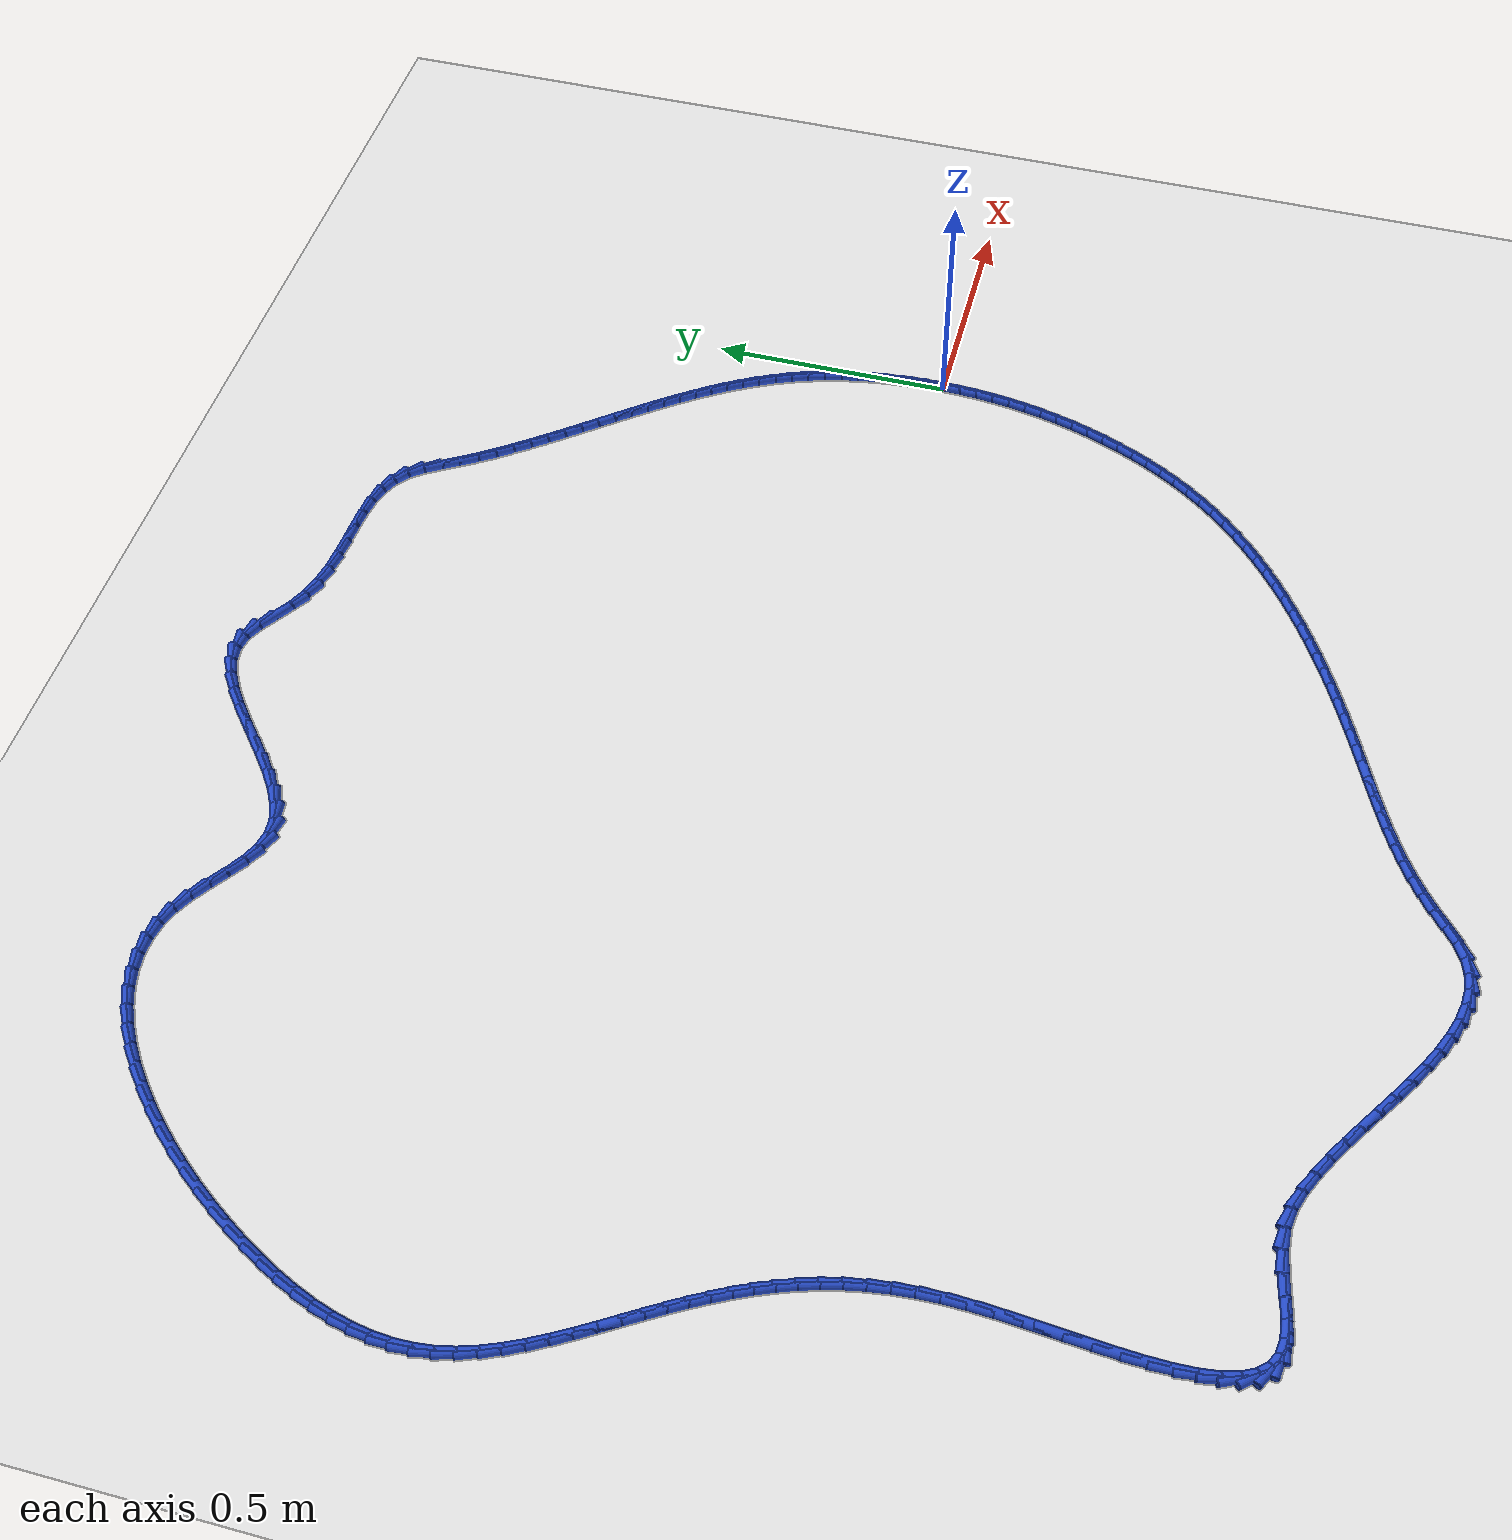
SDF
<sdf version="1.6">
 <world name="default">
  <light name="sun" type="directional">
   <pose>0 0 10 0 -0 0</pose>
   <diffuse>0.8 0.8 0.8 1</diffuse>
   <specular>0.2 0.2 0.2 1</specular>
   <attenuation>
    <range>1000</range>
    <constant>0.9</constant>
    <linear>0.01</linear>
    <quadratic>0.001</quadratic>
   </attenuation>
   <direction>-0.5 0.1 -0.9</direction>
  </light>
  <model name="ground_plane">
   <static>1</static>
   <link name="link">
    <collision name="collision">
     <geometry><plane><normal>0 0 1</normal><size>100 100</size></plane></geometry>
     <surface><friction><ode><mu>100</mu><mu2>50</mu2></ode></friction></surface>
    </collision>
    <visual name="visual">
     <cast_shadows>0</cast_shadows>
     <geometry><plane><normal>0 0 1</normal><size>100 100</size></plane></geometry>
     <material>
      <script><uri>file://media/materials/scripts/gazebo.material</uri><name>Gazebo/WhiteGlow</name></script>
     </material>
    </visual>
   </link>
  </model>
  <gravity>0 0 -9.8</gravity>
  <magnetic_field>6e-06 2.3e-05 -4.2e-05</magnetic_field>
  <atmosphere type="adiabatic"/>
  <physics name="default_physics" default="0" type="ode">
   <max_step_size>0.001</max_step_size>
   <real_time_factor>1</real_time_factor>
   <real_time_update_rate>1000</real_time_update_rate>
  </physics>
  <scene><ambient>0.4 0.4 0.4 1</ambient><background>0.7 0.7 0.7 1</background><shadows>1</shadows></scene>
  <spherical_coordinates>
   <surface_model>EARTH_WGS84</surface_model>
   <latitude_deg>0</latitude_deg>
   <longitude_deg>0</longitude_deg>
   <elevation>0</elevation>
   <heading_deg>0</heading_deg>
  </spherical_coordinates>
  <model name="line">
   <link name="link_0">
    <pose>1.734723475976807e-17 6.938893903907228e-18 0.01 0 1.57 -1.5604815669485337</pose>
    <collision name="collision">
     <geometry><cylinder><radius>0.01</radius><length>0.08</length></cylinder></geometry>
    </collision>
    <visual name="visual">
     <material>
      <script><name>Gazebo/Blue</name><uri>file://media/materials/scripts/gazebo.material</uri></script>
     </material>
     <geometry><cylinder><radius>0.01</radius><length>0.08</length></cylinder></geometry>
    </visual>
   </link>
   <link name="link_1">
    <pose>-0.00038702410670637374 0.03752005734090273 0.01 0 1.57 -1.524317743062453</pose>
    <collision name="collision">
     <geometry><cylinder><radius>0.01</radius><length>0.08</length></cylinder></geometry>
    </collision>
    <visual name="visual">
     <material>
      <script><name>Gazebo/Blue</name><uri>file://media/materials/scripts/gazebo.material</uri></script>
     </material>
     <geometry><cylinder><radius>0.01</radius><length>0.08</length></cylinder></geometry>
    </visual>
   </link>
   <link name="link_2">
    <pose>-0.0021332918375777895 0.07506444760037405 0.01 0 1.57 -1.4868718520865138</pose>
    <collision name="collision">
     <geometry><cylinder><radius>0.01</radius><length>0.08</length></cylinder></geometry>
    </collision>
    <visual name="visual">
     <material>
      <script><name>Gazebo/Blue</name><uri>file://media/materials/scripts/gazebo.material</uri></script>
     </material>
     <geometry><cylinder><radius>0.01</radius><length>0.08</length></cylinder></geometry>
    </visual>
   </link>
   <link name="link_3">
    <pose>-0.005283089859301521 0.1125076314728183 0.01 0 1.57 -1.447881875070658</pose>
    <collision name="collision">
     <geometry><cylinder><radius>0.01</radius><length>0.08</length></cylinder></geometry>
    </collision>
    <visual name="visual">
     <material>
      <script><name>Gazebo/Blue</name><uri>file://media/materials/scripts/gazebo.material</uri></script>
     </material>
     <geometry><cylinder><radius>0.01</radius><length>0.08</length></cylinder></geometry>
    </visual>
   </link>
   <link name="link_4">
    <pose>-0.00988070483856485 0.14972406965263976 0.01 0 1.57 -1.4070813392134902</pose>
    <collision name="collision">
     <geometry><cylinder><radius>0.01</radius><length>0.08</length></cylinder></geometry>
    </collision>
    <visual name="visual">
     <material>
      <script><name>Gazebo/Blue</name><uri>file://media/materials/scripts/gazebo.material</uri></script>
     </material>
     <geometry><cylinder><radius>0.01</radius><length>0.08</length></cylinder></geometry>
    </visual>
   </link>
   <link name="link_5">
    <pose>-0.01597042344205507 0.1865882228342427 0.01 0 1.57 -1.3641995270044551</pose>
    <collision name="collision">
     <geometry><cylinder><radius>0.01</radius><length>0.08</length></cylinder></geometry>
    </collision>
    <visual name="visual">
     <material>
      <script><name>Gazebo/Blue</name><uri>file://media/materials/scripts/gazebo.material</uri></script>
     </material>
     <geometry><cylinder><radius>0.01</radius><length>0.08</length></cylinder></geometry>
    </visual>
   </link>
   <link name="link_6">
    <pose>-0.023596532336459454 0.2229745517120315 0.01 0 1.57 -1.3189634490038837</pose>
    <collision name="collision">
     <geometry><cylinder><radius>0.01</radius><length>0.08</length></cylinder></geometry>
    </collision>
    <visual name="visual">
     <material>
      <script><name>Gazebo/Blue</name><uri>file://media/materials/scripts/gazebo.material</uri></script>
     </material>
     <geometry><cylinder><radius>0.01</radius><length>0.08</length></cylinder></geometry>
    </visual>
   </link>
   <link name="link_7">
    <pose>-0.03280331818846533 0.2587575169804106 0.01 0 1.57 -1.2711020888681037</pose>
    <collision name="collision">
     <geometry><cylinder><radius>0.01</radius><length>0.08</length></cylinder></geometry>
    </collision>
    <visual name="visual">
     <material>
      <script><name>Gazebo/Blue</name><uri>file://media/materials/scripts/gazebo.material</uri></script>
     </material>
     <geometry><cylinder><radius>0.01</radius><length>0.08</length></cylinder></geometry>
    </visual>
   </link>
   <link name="link_8">
    <pose>-0.04363506766475993 0.2938115793337841 0.01 0 1.57 -1.2205400924225447</pose>
    <collision name="collision">
     <geometry><cylinder><radius>0.01</radius><length>0.08</length></cylinder></geometry>
    </collision>
    <visual name="visual">
     <material>
      <script><name>Gazebo/Blue</name><uri>file://media/materials/scripts/gazebo.material</uri></script>
     </material>
     <geometry><cylinder><radius>0.01</radius><length>0.08</length></cylinder></geometry>
    </visual>
   </link>
   <link name="link_9">
    <pose>-0.056131040771296575 0.32801723679350003 0.01 0 1.57 -1.1704785263223896</pose>
    <collision name="collision">
     <geometry><cylinder><radius>0.01</radius><length>0.08</length></cylinder></geometry>
    </collision>
    <visual name="visual">
     <material>
      <script><name>Gazebo/Blue</name><uri>file://media/materials/scripts/gazebo.material</uri></script>
     </material>
     <geometry><cylinder><radius>0.01</radius><length>0.08</length></cylinder></geometry>
    </visual>
   </link>
   <link name="link_10">
    <pose>-0.07024144840245235 0.3613619408096501 0.01 0 1.57 -1.1240644393775192</pose>
    <collision name="collision">
     <geometry><cylinder><radius>0.01</radius><length>0.08</length></cylinder></geometry>
    </collision>
    <visual name="visual">
     <material>
      <script><name>Gazebo/Blue</name><uri>file://media/materials/scripts/gazebo.material</uri></script>
     </material>
     <geometry><cylinder><radius>0.01</radius><length>0.08</length></cylinder></geometry>
    </visual>
   </link>
   <link name="link_11">
    <pose>-0.08584010530134929 0.39392489928194013 0.01 0 1.57 -1.0817084656119904</pose>
    <collision name="collision">
     <geometry><cylinder><radius>0.01</radius><length>0.08</length></cylinder></geometry>
    </collision>
    <visual name="visual">
     <material>
      <script><name>Gazebo/Blue</name><uri>file://media/materials/scripts/gazebo.material</uri></script>
     </material>
     <geometry><cylinder><radius>0.01</radius><length>0.08</length></cylinder></geometry>
    </visual>
   </link>
   <link name="link_12">
    <pose>-0.10279834878915926 0.42578829564534365 0.01 0 1.57 -1.0436220101364924</pose>
    <collision name="collision">
     <geometry><cylinder><radius>0.01</radius><length>0.08</length></cylinder></geometry>
    </collision>
    <visual name="visual">
     <material>
      <script><name>Gazebo/Blue</name><uri>file://media/materials/scripts/gazebo.material</uri></script>
     </material>
     <geometry><cylinder><radius>0.01</radius><length>0.08</length></cylinder></geometry>
    </visual>
   </link>
   <link name="link_13">
    <pose>-0.1209875161870541 0.4570343133348337 0.01 0 1.57 -1.0099251140251995</pose>
    <collision name="collision">
     <geometry><cylinder><radius>0.01</radius><length>0.08</length></cylinder></geometry>
    </collision>
    <visual name="visual">
     <material>
      <script><name>Gazebo/Blue</name><uri>file://media/materials/scripts/gazebo.material</uri></script>
     </material>
     <geometry><cylinder><radius>0.01</radius><length>0.08</length></cylinder></geometry>
    </visual>
   </link>
   <link name="link_14">
    <pose>-0.14027894481620568 0.48774513578538364 0.01 0 1.57 -0.9806653728320486</pose>
    <collision name="collision">
     <geometry><cylinder><radius>0.01</radius><length>0.08</length></cylinder></geometry>
    </collision>
    <visual name="visual">
     <material>
      <script><name>Gazebo/Blue</name><uri>file://media/materials/scripts/gazebo.material</uri></script>
     </material>
     <geometry><cylinder><radius>0.01</radius><length>0.08</length></cylinder></geometry>
    </visual>
   </link>
   <link name="link_15">
    <pose>-0.16054397199778578 0.5180029464319668 0.01 0 1.57 -0.9558370981229501</pose>
    <collision name="collision">
     <geometry><cylinder><radius>0.01</radius><length>0.08</length></cylinder></geometry>
    </collision>
    <visual name="visual">
     <material>
      <script><name>Gazebo/Blue</name><uri>file://media/materials/scripts/gazebo.material</uri></script>
     </material>
     <geometry><cylinder><radius>0.01</radius><length>0.08</length></cylinder></geometry>
    </visual>
   </link>
   <link name="link_16">
    <pose>-0.1816539350529663 0.5478899287095563 0.01 0 1.57 -0.9353988658795472</pose>
    <collision name="collision">
     <geometry><cylinder><radius>0.01</radius><length>0.08</length></cylinder></geometry>
    </collision>
    <visual name="visual">
     <material>
      <script><name>Gazebo/Blue</name><uri>file://media/materials/scripts/gazebo.material</uri></script>
     </material>
     <geometry><cylinder><radius>0.01</radius><length>0.08</length></cylinder></geometry>
    </visual>
   </link>
   <link name="link_17">
    <pose>-0.203480171302919 0.5774882660531255 0.01 0 1.57 -0.9192884241856238</pose>
    <collision name="collision">
     <geometry><cylinder><radius>0.01</radius><length>0.08</length></cylinder></geometry>
    </collision>
    <visual name="visual">
     <material>
      <script><name>Gazebo/Blue</name><uri>file://media/materials/scripts/gazebo.material</uri></script>
     </material>
     <geometry><cylinder><radius>0.01</radius><length>0.08</length></cylinder></geometry>
    </visual>
   </link>
   <link name="link_18">
    <pose>-0.22589401806881582 0.6068801418976478 0.01 0 1.57 -0.9074345662001893</pose>
    <collision name="collision">
     <geometry><cylinder><radius>0.01</radius><length>0.08</length></cylinder></geometry>
    </collision>
    <visual name="visual">
     <material>
      <script><name>Gazebo/Blue</name><uri>file://media/materials/scripts/gazebo.material</uri></script>
     </material>
     <geometry><cylinder><radius>0.01</radius><length>0.08</length></cylinder></geometry>
    </visual>
   </link>
   <link name="link_19">
    <pose>-0.2487668126718285 0.6361477396780961 0.01 0 1.57 -0.8997659828083222</pose>
    <collision name="collision">
     <geometry><cylinder><radius>0.01</radius><length>0.08</length></cylinder></geometry>
    </collision>
    <visual name="visual">
     <material>
      <script><name>Gazebo/Blue</name><uri>file://media/materials/scripts/gazebo.material</uri></script>
     </material>
     <geometry><cylinder><radius>0.01</radius><length>0.08</length></cylinder></geometry>
    </visual>
   </link>
   <link name="link_20">
    <pose>-0.271969892433129 0.6653732428294441 0.01 0 1.57 -0.8962173230918993</pose>
    <collision name="collision">
     <geometry><cylinder><radius>0.01</radius><length>0.08</length></cylinder></geometry>
    </collision>
    <visual name="visual">
     <material>
      <script><name>Gazebo/Blue</name><uri>file://media/materials/scripts/gazebo.material</uri></script>
     </material>
     <geometry><cylinder><radius>0.01</radius><length>0.08</length></cylinder></geometry>
    </visual>
   </link>
   <link name="link_21">
    <pose>-0.29537459467388916 0.694638834786665 0.01 0 1.57 -0.8967327629448139</pose>
    <collision name="collision">
     <geometry><cylinder><radius>0.01</radius><length>0.08</length></cylinder></geometry>
    </collision>
    <visual name="visual">
     <material>
      <script><name>Gazebo/Blue</name><uri>file://media/materials/scripts/gazebo.material</uri></script>
     </material>
     <geometry><cylinder><radius>0.01</radius><length>0.08</length></cylinder></geometry>
    </visual>
   </link>
   <link name="link_22">
    <pose>-0.3188522567152807 0.7240266989847319 0.01 0 1.57 -0.9012673655954462</pose>
    <collision name="collision">
     <geometry><cylinder><radius>0.01</radius><length>0.08</length></cylinder></geometry>
    </collision>
    <visual name="visual">
     <material>
      <script><name>Gazebo/Blue</name><uri>file://media/materials/scripts/gazebo.material</uri></script>
     </material>
     <geometry><cylinder><radius>0.01</radius><length>0.08</length></cylinder></geometry>
    </visual>
   </link>
   <link name="link_23">
    <pose>-0.34227421587847556 0.7536190188586184 0.01 0 1.57 -0.9097864556969446</pose>
    <collision name="collision">
     <geometry><cylinder><radius>0.01</radius><length>0.08</length></cylinder></geometry>
    </collision>
    <visual name="visual">
     <material>
      <script><name>Gazebo/Blue</name><uri>file://media/materials/scripts/gazebo.material</uri></script>
     </material>
     <geometry><cylinder><radius>0.01</radius><length>0.08</length></cylinder></geometry>
    </visual>
   </link>
   <link name="link_24">
    <pose>-0.36551180948464557 0.7834979778432972 0.01 0 1.57 -0.9222631534774657</pose>
    <collision name="collision">
     <geometry><cylinder><radius>0.01</radius><length>0.08</length></cylinder></geometry>
    </collision>
    <visual name="visual">
     <material>
      <script><name>Gazebo/Blue</name><uri>file://media/materials/scripts/gazebo.material</uri></script>
     </material>
     <geometry><cylinder><radius>0.01</radius><length>0.08</length></cylinder></geometry>
    </visual>
   </link>
   <link name="link_25">
    <pose>-0.38843637485496246 0.813745759373742 0.01 0 1.57 -0.9386741516493533</pose>
    <collision name="collision">
     <geometry><cylinder><radius>0.01</radius><length>0.08</length></cylinder></geometry>
    </collision>
    <visual name="visual">
     <material>
      <script><name>Gazebo/Blue</name><uri>file://media/materials/scripts/gazebo.material</uri></script>
     </material>
     <geometry><cylinder><radius>0.01</radius><length>0.08</length></cylinder></geometry>
    </visual>
   </link>
   <link name="link_26">
    <pose>-0.41091924931059826 0.8444445468849261 0.01 0 1.57 -0.9589937853042427</pose>
    <collision name="collision">
     <geometry><cylinder><radius>0.01</radius><length>0.08</length></cylinder></geometry>
    </collision>
    <visual name="visual">
     <material>
      <script><name>Gazebo/Blue</name><uri>file://media/materials/scripts/gazebo.material</uri></script>
     </material>
     <geometry><cylinder><radius>0.01</radius><length>0.08</length></cylinder></geometry>
    </visual>
   </link>
   <link name="link_27">
    <pose>-0.43283177017272473 0.8756765238118227 0.01 0 1.57 -0.9831864619062438</pose>
    <collision name="collision">
     <geometry><cylinder><radius>0.01</radius><length>0.08</length></cylinder></geometry>
    </collision>
    <visual name="visual">
     <material>
      <script><name>Gazebo/Blue</name><uri>file://media/materials/scripts/gazebo.material</uri></script>
     </material>
     <geometry><cylinder><radius>0.01</radius><length>0.08</length></cylinder></geometry>
    </visual>
   </link>
   <link name="link_28">
    <pose>-0.45404527476251366 0.907523873589405 0.01 0 1.57 -1.0111976013252622</pose>
    <collision name="collision">
     <geometry><cylinder><radius>0.01</radius><length>0.08</length></cylinder></geometry>
    </collision>
    <visual name="visual">
     <material>
      <script><name>Gazebo/Blue</name><uri>file://media/materials/scripts/gazebo.material</uri></script>
     </material>
     <geometry><cylinder><radius>0.01</radius><length>0.08</length></cylinder></geometry>
    </visual>
   </link>
   <link name="link_29">
    <pose>-0.4744311004011368 0.9400687796526459 0.01 0 1.57 -1.0420186037411419</pose>
    <collision name="collision">
     <geometry><cylinder><radius>0.01</radius><length>0.08</length></cylinder></geometry>
    </collision>
    <visual name="visual">
     <material>
      <script><name>Gazebo/Blue</name><uri>file://media/materials/scripts/gazebo.material</uri></script>
     </material>
     <geometry><cylinder><radius>0.01</radius><length>0.08</length></cylinder></geometry>
    </visual>
   </link>
   <link name="link_30">
    <pose>-0.49388287030590694 0.973360853594182 0.01 0 1.57 -1.0315417846794845</pose>
    <collision name="collision">
     <geometry><cylinder><radius>0.01</radius><length>0.08</length></cylinder></geometry>
    </collision>
    <visual name="visual">
     <material>
      <script><name>Gazebo/Blue</name><uri>file://media/materials/scripts/gazebo.material</uri></script>
     </material>
     <geometry><cylinder><radius>0.01</radius><length>0.08</length></cylinder></geometry>
    </visual>
   </link>
   <link name="link_31">
    <pose>-0.5133546952859124 1.0058997565616263 0.01 0 1.57 -0.9075513861924633</pose>
    <collision name="collision">
     <geometry><cylinder><radius>0.01</radius><length>0.08</length></cylinder></geometry>
    </collision>
    <visual name="visual">
     <material>
      <script><name>Gazebo/Blue</name><uri>file://media/materials/scripts/gazebo.material</uri></script>
     </material>
     <geometry><cylinder><radius>0.01</radius><length>0.08</length></cylinder></geometry>
    </visual>
   </link>
   <link name="link_32">
    <pose>-0.5353023818814912 1.0339903664669332 0.01 0 1.57 -0.6685776298659545</pose>
    <collision name="collision">
     <geometry><cylinder><radius>0.01</radius><length>0.08</length></cylinder></geometry>
    </collision>
    <visual name="visual">
     <material>
      <script><name>Gazebo/Blue</name><uri>file://media/materials/scripts/gazebo.material</uri></script>
     </material>
     <geometry><cylinder><radius>0.01</radius><length>0.08</length></cylinder></geometry>
    </visual>
   </link>
   <link name="link_33">
    <pose>-0.5616491666063063 1.0548027886602451 0.01 0 1.57 -0.4359050235113235</pose>
    <collision name="collision">
     <geometry><cylinder><radius>0.01</radius><length>0.08</length></cylinder></geometry>
    </collision>
    <visual name="visual">
     <material>
      <script><name>Gazebo/Blue</name><uri>file://media/materials/scripts/gazebo.material</uri></script>
     </material>
     <geometry><cylinder><radius>0.01</radius><length>0.08</length></cylinder></geometry>
    </visual>
   </link>
   <link name="link_34">
    <pose>-0.5921295218241447 1.0690001589825353 0.01 0 1.57 -0.25916366139390684</pose>
    <collision name="collision">
     <geometry><cylinder><radius>0.01</radius><length>0.08</length></cylinder></geometry>
    </collision>
    <visual name="visual">
     <material>
      <script><name>Gazebo/Blue</name><uri>file://media/materials/scripts/gazebo.material</uri></script>
     </material>
     <geometry><cylinder><radius>0.01</radius><length>0.08</length></cylinder></geometry>
    </visual>
   </link>
   <link name="link_35">
    <pose>-0.6260151588815508 1.0779841297308712 0.01 0 1.57 -0.14052956637237352</pose>
    <collision name="collision">
     <geometry><cylinder><radius>0.01</radius><length>0.08</length></cylinder></geometry>
    </collision>
    <visual name="visual">
     <material>
      <script><name>Gazebo/Blue</name><uri>file://media/materials/scripts/gazebo.material</uri></script>
     </material>
     <geometry><cylinder><radius>0.01</radius><length>0.08</length></cylinder></geometry>
    </visual>
   </link>
   <link name="link_36">
    <pose>-0.6625777891250685 1.0831563532023205 0.01 0 1.57 -0.07159987669794818</pose>
    <collision name="collision">
     <geometry><cylinder><radius>0.01</radius><length>0.08</length></cylinder></geometry>
    </collision>
    <visual name="visual">
     <material>
      <script><name>Gazebo/Blue</name><uri>file://media/materials/scripts/gazebo.material</uri></script>
     </material>
     <geometry><cylinder><radius>0.01</radius><length>0.08</length></cylinder></geometry>
    </visual>
   </link>
   <link name="link_37">
    <pose>-0.7010891239012431 1.0859184816939504 0.01 0 1.57 -0.04410951643993323</pose>
    <collision name="collision">
     <geometry><cylinder><radius>0.01</radius><length>0.08</length></cylinder></geometry>
    </collision>
    <visual name="visual">
     <material>
      <script><name>Gazebo/Blue</name><uri>file://media/materials/scripts/gazebo.material</uri></script>
     </material>
     <geometry><cylinder><radius>0.01</radius><length>0.08</length></cylinder></geometry>
    </visual>
   </link>
   <link name="link_38">
    <pose>-0.7408208745566187 1.0876721675028287 0.01 0 1.57 -0.05332305982390599</pose>
    <collision name="collision">
     <geometry><cylinder><radius>0.01</radius><length>0.08</length></cylinder></geometry>
    </collision>
    <visual name="visual">
     <material>
      <script><name>Gazebo/Blue</name><uri>file://media/materials/scripts/gazebo.material</uri></script>
     </material>
     <geometry><cylinder><radius>0.01</radius><length>0.08</length></cylinder></geometry>
    </visual>
   </link>
   <link name="link_39">
    <pose>-0.7810447524377395 1.0898190629260223 0.01 0 1.57 -0.09825677529094552</pose>
    <collision name="collision">
     <geometry><cylinder><radius>0.01</radius><length>0.08</length></cylinder></geometry>
    </collision>
    <visual name="visual">
     <material>
      <script><name>Gazebo/Blue</name><uri>file://media/materials/scripts/gazebo.material</uri></script>
     </material>
     <geometry><cylinder><radius>0.01</radius><length>0.08</length></cylinder></geometry>
    </visual>
   </link>
   <link name="link_40">
    <pose>-0.8210324688911506 1.093760820260599 0.01 0 1.57 -0.18092321638941208</pose>
    <collision name="collision">
     <geometry><cylinder><radius>0.01</radius><length>0.08</length></cylinder></geometry>
    </collision>
    <visual name="visual">
     <material>
      <script><name>Gazebo/Blue</name><uri>file://media/materials/scripts/gazebo.material</uri></script>
     </material>
     <geometry><cylinder><radius>0.01</radius><length>0.08</length></cylinder></geometry>
    </visual>
   </link>
   <link name="link_41">
    <pose>-0.8600557352633956 1.1008990918036266 0.01 0 1.57 -0.3046080697102999</pose>
    <collision name="collision">
     <geometry><cylinder><radius>0.01</radius><length>0.08</length></cylinder></geometry>
    </collision>
    <visual name="visual">
     <material>
      <script><name>Gazebo/Blue</name><uri>file://media/materials/scripts/gazebo.material</uri></script>
     </material>
     <geometry><cylinder><radius>0.01</radius><length>0.08</length></cylinder></geometry>
    </visual>
   </link>
   <link name="link_42">
    <pose>-0.8973862629010194 1.1126355298521724 0.01 0 1.57 -0.4662531983001789</pose>
    <collision name="collision">
     <geometry><cylinder><radius>0.01</radius><length>0.08</length></cylinder></geometry>
    </collision>
    <visual name="visual">
     <material>
      <script><name>Gazebo/Blue</name><uri>file://media/materials/scripts/gazebo.material</uri></script>
     </material>
     <geometry><cylinder><radius>0.01</radius><length>0.08</length></cylinder></geometry>
    </visual>
   </link>
   <link name="link_43">
    <pose>-0.9323342719702692 1.1302235083274457 0.01 0 1.57 -0.5834662010759961</pose>
    <collision name="collision">
     <geometry><cylinder><radius>0.01</radius><length>0.08</length></cylinder></geometry>
    </collision>
    <visual name="visual">
     <material>
      <script><name>Gazebo/Blue</name><uri>file://media/materials/scripts/gazebo.material</uri></script>
     </material>
     <geometry><cylinder><radius>0.01</radius><length>0.08</length></cylinder></geometry>
    </visual>
   </link>
   <link name="link_44">
    <pose>-0.9650193268606378 1.1518000177387655 0.01 0 1.57 -0.5850541811218599</pose>
    <collision name="collision">
     <geometry><cylinder><radius>0.01</radius><length>0.08</length></cylinder></geometry>
    </collision>
    <visual name="visual">
     <material>
      <script><name>Gazebo/Blue</name><uri>file://media/materials/scripts/gazebo.material</uri></script>
     </material>
     <geometry><cylinder><radius>0.01</radius><length>0.08</length></cylinder></geometry>
    </visual>
   </link>
   <link name="link_45">
    <pose>-0.9963300588764114 1.1725407531329517 0.01 0 1.57 -0.4515366577397495</pose>
    <collision name="collision">
     <geometry><cylinder><radius>0.01</radius><length>0.08</length></cylinder></geometry>
    </collision>
    <visual name="visual">
     <material>
      <script><name>Gazebo/Blue</name><uri>file://media/materials/scripts/gazebo.material</uri></script>
     </material>
     <geometry><cylinder><radius>0.01</radius><length>0.08</length></cylinder></geometry>
    </visual>
   </link>
   <link name="link_46">
    <pose>-1.0271855460992418 1.1875041741096501 0.01 0 1.57 -0.15753588134242896</pose>
    <collision name="collision">
     <geometry><cylinder><radius>0.01</radius><length>0.08</length></cylinder></geometry>
    </collision>
    <visual name="visual">
     <material>
      <script><name>Gazebo/Blue</name><uri>file://media/materials/scripts/gazebo.material</uri></script>
     </material>
     <geometry><cylinder><radius>0.01</radius><length>0.08</length></cylinder></geometry>
    </visual>
   </link>
   <link name="link_47">
    <pose>-1.058397586988972 1.1924622744759585 0.01 0 1.57 0.15557918786977865</pose>
    <collision name="collision">
     <geometry><cylinder><radius>0.01</radius><length>0.08</length></cylinder></geometry>
    </collision>
    <visual name="visual">
     <material>
      <script><name>Gazebo/Blue</name><uri>file://media/materials/scripts/gazebo.material</uri></script>
     </material>
     <geometry><cylinder><radius>0.01</radius><length>0.08</length></cylinder></geometry>
    </visual>
   </link>
   <link name="link_48">
    <pose>-1.0901318044764465 1.1874848665452247 0.01 0 1.57 0.39035812778094003</pose>
    <collision name="collision">
     <geometry><cylinder><radius>0.01</radius><length>0.08</length></cylinder></geometry>
    </collision>
    <visual name="visual">
     <material>
      <script><name>Gazebo/Blue</name><uri>file://media/materials/scripts/gazebo.material</uri></script>
     </material>
     <geometry><cylinder><radius>0.01</radius><length>0.08</length></cylinder></geometry>
    </visual>
   </link>
   <link name="link_49">
    <pose>-1.122313056393677 1.1742431304495673 0.01 0 1.57 0.54718012473671</pose>
    <collision name="collision">
     <geometry><cylinder><radius>0.01</radius><length>0.08</length></cylinder></geometry>
    </collision>
    <visual name="visual">
     <material>
      <script><name>Gazebo/Blue</name><uri>file://media/materials/scripts/gazebo.material</uri></script>
     </material>
     <geometry><cylinder><radius>0.01</radius><length>0.08</length></cylinder></geometry>
    </visual>
   </link>
   <link name="link_50">
    <pose>-1.1548657924680907 1.1544109606910593 0.01 0 1.57 0.6456836770044759</pose>
    <collision name="collision">
     <geometry><cylinder><radius>0.01</radius><length>0.08</length></cylinder></geometry>
    </collision>
    <visual name="visual">
     <material>
      <script><name>Gazebo/Blue</name><uri>file://media/materials/scripts/gazebo.material</uri></script>
     </material>
     <geometry><cylinder><radius>0.01</radius><length>0.08</length></cylinder></geometry>
    </visual>
   </link>
   <link name="link_51">
    <pose>-1.1877144624271152 1.129662251771773 0.01 0 1.57 0.702430429451977</pose>
    <collision name="collision">
     <geometry><cylinder><radius>0.01</radius><length>0.08</length></cylinder></geometry>
    </collision>
    <visual name="visual">
     <material>
      <script><name>Gazebo/Blue</name><uri>file://media/materials/scripts/gazebo.material</uri></script>
     </material>
     <geometry><cylinder><radius>0.01</radius><length>0.08</length></cylinder></geometry>
    </visual>
   </link>
   <link name="link_52">
    <pose>-1.2207835159981775 1.101670898193779 0.01 0 1.57 0.7272583935490622</pose>
    <collision name="collision">
     <geometry><cylinder><radius>0.01</radius><length>0.08</length></cylinder></geometry>
    </collision>
    <visual name="visual">
     <material>
      <script><name>Gazebo/Blue</name><uri>file://media/materials/scripts/gazebo.material</uri></script>
     </material>
     <geometry><cylinder><radius>0.01</radius><length>0.08</length></cylinder></geometry>
    </visual>
   </link>
   <link name="link_53">
    <pose>-1.2539974029087042 1.0721107944591506 0.01 0 1.57 0.7244548420812014</pose>
    <collision name="collision">
     <geometry><cylinder><radius>0.01</radius><length>0.08</length></cylinder></geometry>
    </collision>
    <visual name="visual">
     <material>
      <script><name>Gazebo/Blue</name><uri>file://media/materials/scripts/gazebo.material</uri></script>
     </material>
     <geometry><cylinder><radius>0.01</radius><length>0.08</length></cylinder></geometry>
    </visual>
   </link>
   <link name="link_54">
    <pose>-1.287280572886123 1.0426558350699588 0.01 0 1.57 0.6937650496179695</pose>
    <collision name="collision">
     <geometry><cylinder><radius>0.01</radius><length>0.08</length></cylinder></geometry>
    </collision>
    <visual name="visual">
     <material>
      <script><name>Gazebo/Blue</name><uri>file://media/materials/scripts/gazebo.material</uri></script>
     </material>
     <geometry><cylinder><radius>0.01</radius><length>0.08</length></cylinder></geometry>
    </visual>
   </link>
   <link name="link_55">
    <pose>-1.3205574756578609 1.014979914528276 0.01 0 1.57 0.6303925082494315</pose>
    <collision name="collision">
     <geometry><cylinder><radius>0.01</radius><length>0.08</length></cylinder></geometry>
    </collision>
    <visual name="visual">
     <material>
      <script><name>Gazebo/Blue</name><uri>file://media/materials/scripts/gazebo.material</uri></script>
     </material>
     <geometry><cylinder><radius>0.01</radius><length>0.08</length></cylinder></geometry>
    </visual>
   </link>
   <link name="link_56">
    <pose>-1.3537525609513443 0.990756927336174 0.01 0 1.57 0.524094072703477</pose>
    <collision name="collision">
     <geometry><cylinder><radius>0.01</radius><length>0.08</length></cylinder></geometry>
    </collision>
    <visual name="visual">
     <material>
      <script><name>Gazebo/Blue</name><uri>file://media/materials/scripts/gazebo.material</uri></script>
     </material>
     <geometry><cylinder><radius>0.01</radius><length>0.08</length></cylinder></geometry>
    </visual>
   </link>
   <link name="link_57">
    <pose>-1.3867902784940016 0.9716607679957248 0.01 0 1.57 0.3586006119283363</pose>
    <collision name="collision">
     <geometry><cylinder><radius>0.01</radius><length>0.08</length></cylinder></geometry>
    </collision>
    <visual name="visual">
     <material>
      <script><name>Gazebo/Blue</name><uri>file://media/materials/scripts/gazebo.material</uri></script>
     </material>
     <geometry><cylinder><radius>0.01</radius><length>0.08</length></cylinder></geometry>
    </visual>
   </link>
   <link name="link_58">
    <pose>-1.4195950780132582 0.9593653310090001 0.01 0 1.57 0.11703961110177963</pose>
    <collision name="collision">
     <geometry><cylinder><radius>0.01</radius><length>0.08</length></cylinder></geometry>
    </collision>
    <visual name="visual">
     <material>
      <script><name>Gazebo/Blue</name><uri>file://media/materials/scripts/gazebo.material</uri></script>
     </material>
     <geometry><cylinder><radius>0.01</radius><length>0.08</length></cylinder></geometry>
    </visual>
   </link>
   <link name="link_59">
    <pose>-1.4520914092365431 0.955544510878072 0.01 0 1.57 -0.18950009768322418</pose>
    <collision name="collision">
     <geometry><cylinder><radius>0.01</radius><length>0.08</length></cylinder></geometry>
    </collision>
    <visual name="visual">
     <material>
      <script><name>Gazebo/Blue</name><uri>file://media/materials/scripts/gazebo.material</uri></script>
     </material>
     <geometry><cylinder><radius>0.01</radius><length>0.08</length></cylinder></geometry>
    </visual>
   </link>
   <link name="link_60">
    <pose>-1.4842132125528649 0.9617055207821021 0.01 0 1.57 -0.44080182856185796</pose>
    <collision name="collision">
     <geometry><cylinder><radius>0.01</radius><length>0.08</length></cylinder></geometry>
    </collision>
    <visual name="visual">
     <material>
      <script><name>Gazebo/Blue</name><uri>file://media/materials/scripts/gazebo.material</uri></script>
     </material>
     <geometry><cylinder><radius>0.01</radius><length>0.08</length></cylinder></geometry>
    </visual>
   </link>
   <link name="link_61">
    <pose>-1.516044369842912 0.9767222015085499 0.01 0 1.57 -0.5766342609409975</pose>
    <collision name="collision">
     <geometry><cylinder><radius>0.01</radius><length>0.08</length></cylinder></geometry>
    </collision>
    <visual name="visual">
     <material>
      <script><name>Gazebo/Blue</name><uri>file://media/materials/scripts/gazebo.material</uri></script>
     </material>
     <geometry><cylinder><radius>0.01</radius><length>0.08</length></cylinder></geometry>
    </visual>
   </link>
   <link name="link_62">
    <pose>-1.5477883851003071 0.9973675105861908 0.01 0 1.57 -0.6249845077806354</pose>
    <collision name="collision">
     <geometry><cylinder><radius>0.01</radius><length>0.08</length></cylinder></geometry>
    </collision>
    <visual name="visual">
     <material>
      <script><name>Gazebo/Blue</name><uri>file://media/materials/scripts/gazebo.material</uri></script>
     </material>
     <geometry><cylinder><radius>0.01</radius><length>0.08</length></cylinder></geometry>
    </visual>
   </link>
   <link name="link_63">
    <pose>-1.5796520919291819 1.0203559287053485 0.01 0 1.57 -0.6004968038015023</pose>
    <collision name="collision">
     <geometry><cylinder><radius>0.01</radius><length>0.08</length></cylinder></geometry>
    </collision>
    <visual name="visual">
     <material>
      <script><name>Gazebo/Blue</name><uri>file://media/materials/scripts/gazebo.material</uri></script>
     </material>
     <geometry><cylinder><radius>0.01</radius><length>0.08</length></cylinder></geometry>
    </visual>
   </link>
   <link name="link_64">
    <pose>-1.611842323933668 1.0424019365563462 0.01 0 1.57 -0.4995642378201424</pose>
    <collision name="collision">
     <geometry><cylinder><radius>0.01</radius><length>0.08</length></cylinder></geometry>
    </collision>
    <visual name="visual">
     <material>
      <script><name>Gazebo/Blue</name><uri>file://media/materials/scripts/gazebo.material</uri></script>
     </material>
     <geometry><cylinder><radius>0.01</radius><length>0.08</length></cylinder></geometry>
    </visual>
   </link>
   <link name="link_65">
    <pose>-1.644562260707341 1.060258410495363 0.01 0 1.57 -0.34372883033076274</pose>
    <collision name="collision">
     <geometry><cylinder><radius>0.01</radius><length>0.08</length></cylinder></geometry>
    </collision>
    <visual name="visual">
     <material>
      <script><name>Gazebo/Blue</name><uri>file://media/materials/scripts/gazebo.material</uri></script>
     </material>
     <geometry><cylinder><radius>0.01</radius><length>0.08</length></cylinder></geometry>
    </visual>
   </link>
   <link name="link_66">
    <pose>-1.6778720439172352 1.0721812429063255 0.01 0 1.57 -0.18165765670270456</pose>
    <collision name="collision">
     <geometry><cylinder><radius>0.01</radius><length>0.08</length></cylinder></geometry>
    </collision>
    <visual name="visual">
     <material>
      <script><name>Gazebo/Blue</name><uri>file://media/materials/scripts/gazebo.material</uri></script>
     </material>
     <geometry><cylinder><radius>0.01</radius><length>0.08</length></cylinder></geometry>
    </visual>
   </link>
   <link name="link_67">
    <pose>-1.7116454301469795 1.0783848260931965 0.01 0 1.57 -0.024343207805434485</pose>
    <collision name="collision">
     <geometry><cylinder><radius>0.01</radius><length>0.08</length></cylinder></geometry>
    </collision>
    <visual name="visual">
     <material>
      <script><name>Gazebo/Blue</name><uri>file://media/materials/scripts/gazebo.material</uri></script>
     </material>
     <geometry><cylinder><radius>0.01</radius><length>0.08</length></cylinder></geometry>
    </visual>
   </link>
   <link name="link_68">
    <pose>-1.7457436616683435 1.0792150504301001 0.01 0 1.57 0.12181842004860759</pose>
    <collision name="collision">
     <geometry><cylinder><radius>0.01</radius><length>0.08</length></cylinder></geometry>
    </collision>
    <visual name="visual">
     <material>
      <script><name>Gazebo/Blue</name><uri>file://media/materials/scripts/gazebo.material</uri></script>
     </material>
     <geometry><cylinder><radius>0.01</radius><length>0.08</length></cylinder></geometry>
    </visual>
   </link>
   <link name="link_69">
    <pose>-1.7800279807530974 1.0750178062911597 0.01 0 1.57 0.2530742193766821</pose>
    <collision name="collision">
     <geometry><cylinder><radius>0.01</radius><length>0.08</length></cylinder></geometry>
    </collision>
    <visual name="visual">
     <material>
      <script><name>Gazebo/Blue</name><uri>file://media/materials/scripts/gazebo.material</uri></script>
     </material>
     <geometry><cylinder><radius>0.01</radius><length>0.08</length></cylinder></geometry>
    </visual>
   </link>
   <link name="link_70">
    <pose>-1.8143596296730113 1.0661389840504993 0.01 0 1.57 0.368323148087801</pose>
    <collision name="collision">
     <geometry><cylinder><radius>0.01</radius><length>0.08</length></cylinder></geometry>
    </collision>
    <visual name="visual">
     <material>
      <script><name>Gazebo/Blue</name><uri>file://media/materials/scripts/gazebo.material</uri></script>
     </material>
     <geometry><cylinder><radius>0.01</radius><length>0.08</length></cylinder></geometry>
    </visual>
   </link>
   <link name="link_71">
    <pose>-1.8485998506998549 1.0529244740822434 0.01 0 1.57 0.4683243968012774</pose>
    <collision name="collision">
     <geometry><cylinder><radius>0.01</radius><length>0.08</length></cylinder></geometry>
    </collision>
    <visual name="visual">
     <material>
      <script><name>Gazebo/Blue</name><uri>file://media/materials/scripts/gazebo.material</uri></script>
     </material>
     <geometry><cylinder><radius>0.01</radius><length>0.08</length></cylinder></geometry>
    </visual>
   </link>
   <link name="link_72">
    <pose>-1.8826098861054001 1.0357201667605145 0.01 0 1.57 0.5547968144490095</pose>
    <collision name="collision">
     <geometry><cylinder><radius>0.01</radius><length>0.08</length></cylinder></geometry>
    </collision>
    <visual name="visual">
     <material>
      <script><name>Gazebo/Blue</name><uri>file://media/materials/scripts/gazebo.material</uri></script>
     </material>
     <geometry><cylinder><radius>0.01</radius><length>0.08</length></cylinder></geometry>
    </visual>
   </link>
   <link name="link_73">
    <pose>-1.9162509781614152 1.0148719524594372 0.01 0 1.57 0.6297671901206277</pose>
    <collision name="collision">
     <geometry><cylinder><radius>0.01</radius><length>0.08</length></cylinder></geometry>
    </collision>
    <visual name="visual">
     <material>
      <script><name>Gazebo/Blue</name><uri>file://media/materials/scripts/gazebo.material</uri></script>
     </material>
     <geometry><cylinder><radius>0.01</radius><length>0.08</length></cylinder></geometry>
    </visual>
   </link>
   <link name="link_74">
    <pose>-1.949384369139671 0.9907257215531348 0.01 0 1.57 0.6952088441628442</pose>
    <collision name="collision">
     <geometry><cylinder><radius>0.01</radius><length>0.08</length></cylinder></geometry>
    </collision>
    <visual name="visual">
     <material>
      <script><name>Gazebo/Blue</name><uri>file://media/materials/scripts/gazebo.material</uri></script>
     </material>
     <geometry><cylinder><radius>0.01</radius><length>0.08</length></cylinder></geometry>
    </visual>
   </link>
   <link name="link_75">
    <pose>-1.9818713013119378 0.9636273644157314 0.01 0 1.57 0.7528865374459031</pose>
    <collision name="collision">
     <geometry><cylinder><radius>0.01</radius><length>0.08</length></cylinder></geometry>
    </collision>
    <visual name="visual">
     <material>
      <script><name>Gazebo/Blue</name><uri>file://media/materials/scripts/gazebo.material</uri></script>
     </material>
     <geometry><cylinder><radius>0.01</radius><length>0.08</length></cylinder></geometry>
    </visual>
   </link>
   <link name="link_76">
    <pose>-2.013573016949985 0.9339227714213503 0.01 0 1.57 0.8043175887512058</pose>
    <collision name="collision">
     <geometry><cylinder><radius>0.01</radius><length>0.08</length></cylinder></geometry>
    </collision>
    <visual name="visual">
     <material>
      <script><name>Gazebo/Blue</name><uri>file://media/materials/scripts/gazebo.material</uri></script>
     </material>
     <geometry><cylinder><radius>0.01</radius><length>0.08</length></cylinder></geometry>
    </visual>
   </link>
   <link name="link_77">
    <pose>-2.044350758325583 0.9019578329441158 0.01 0 1.57 0.8507883055800376</pose>
    <collision name="collision">
     <geometry><cylinder><radius>0.01</radius><length>0.08</length></cylinder></geometry>
    </collision>
    <visual name="visual">
     <material>
      <script><name>Gazebo/Blue</name><uri>file://media/materials/scripts/gazebo.material</uri></script>
     </material>
     <geometry><cylinder><radius>0.01</radius><length>0.08</length></cylinder></geometry>
    </visual>
   </link>
   <link name="link_78">
    <pose>-2.074065767710503 0.8680784393581514 0.01 0 1.57 0.893392221034686</pose>
    <collision name="collision">
     <geometry><cylinder><radius>0.01</radius><length>0.08</length></cylinder></geometry>
    </collision>
    <visual name="visual">
     <material>
      <script><name>Gazebo/Blue</name><uri>file://media/materials/scripts/gazebo.material</uri></script>
     </material>
     <geometry><cylinder><radius>0.01</radius><length>0.08</length></cylinder></geometry>
    </visual>
   </link>
   <link name="link_79">
    <pose>-2.1025792873765137 0.8326304810375809 0.01 0 1.57 0.9330742754965439</pose>
    <collision name="collision">
     <geometry><cylinder><radius>0.01</radius><length>0.08</length></cylinder></geometry>
    </collision>
    <visual name="visual">
     <material>
      <script><name>Gazebo/Blue</name><uri>file://media/materials/scripts/gazebo.material</uri></script>
     </material>
     <geometry><cylinder><radius>0.01</radius><length>0.08</length></cylinder></geometry>
    </visual>
   </link>
   <link name="link_80">
    <pose>-2.129752559595386 0.7959598483565278 0.01 0 1.57 0.9706748366419309</pose>
    <collision name="collision">
     <geometry><cylinder><radius>0.01</radius><length>0.08</length></cylinder></geometry>
    </collision>
    <visual name="visual">
     <material>
      <script><name>Gazebo/Blue</name><uri>file://media/materials/scripts/gazebo.material</uri></script>
     </material>
     <geometry><cylinder><radius>0.01</radius><length>0.08</length></cylinder></geometry>
    </visual>
   </link>
   <link name="link_81">
    <pose>-2.1554468266388893 0.7584124316891162 0.01 0 1.57 1.0069725067876298</pose>
    <collision name="collision">
     <geometry><cylinder><radius>0.01</radius><length>0.08</length></cylinder></geometry>
    </collision>
    <visual name="visual">
     <material>
      <script><name>Gazebo/Blue</name><uri>file://media/materials/scripts/gazebo.material</uri></script>
     </material>
     <geometry><cylinder><radius>0.01</radius><length>0.08</length></cylinder></geometry>
    </visual>
   </link>
   <link name="link_82">
    <pose>-2.1795233307787947 0.7203341214094698 0.01 0 1.57 1.0427273910908879</pose>
    <collision name="collision">
     <geometry><cylinder><radius>0.01</radius><length>0.08</length></cylinder></geometry>
    </collision>
    <visual name="visual">
     <material>
      <script><name>Gazebo/Blue</name><uri>file://media/materials/scripts/gazebo.material</uri></script>
     </material>
     <geometry><cylinder><radius>0.01</radius><length>0.08</length></cylinder></geometry>
    </visual>
   </link>
   <link name="link_83">
    <pose>-2.201843314286871 0.6820708078917123 0.01 0 1.57 1.0787299858051516</pose>
    <collision name="collision">
     <geometry><cylinder><radius>0.01</radius><length>0.08</length></cylinder></geometry>
    </collision>
    <visual name="visual">
     <material>
      <script><name>Gazebo/Blue</name><uri>file://media/materials/scripts/gazebo.material</uri></script>
     </material>
     <geometry><cylinder><radius>0.01</radius><length>0.08</length></cylinder></geometry>
    </visual>
   </link>
   <link name="link_84">
    <pose>-2.222268008583826 0.6439682551880569 0.01 0 1.57 1.1169397786292758</pose>
    <collision name="collision">
     <geometry><cylinder><radius>0.01</radius><length>0.08</length></cylinder></geometry>
    </collision>
    <visual name="visual">
     <material>
      <script><name>Gazebo/Blue</name><uri>file://media/materials/scripts/gazebo.material</uri></script>
     </material>
     <geometry><cylinder><radius>0.01</radius><length>0.08</length></cylinder></geometry>
    </visual>
   </link>
   <link name="link_85">
    <pose>-2.240651079986755 0.6062841587162477 0.01 0 1.57 1.161150256735616</pose>
    <collision name="collision">
     <geometry><cylinder><radius>0.01</radius><length>0.08</length></cylinder></geometry>
    </collision>
    <visual name="visual">
     <material>
      <script><name>Gazebo/Blue</name><uri>file://media/materials/scripts/gazebo.material</uri></script>
     </material>
     <geometry><cylinder><radius>0.01</radius><length>0.08</length></cylinder></geometry>
    </visual>
   </link>
   <link name="link_86">
    <pose>-2.256825405246102 0.5690341935806772 0.01 0 1.57 1.2125159011337443</pose>
    <collision name="collision">
     <geometry><cylinder><radius>0.01</radius><length>0.08</length></cylinder></geometry>
    </collision>
    <visual name="visual">
     <material>
      <script><name>Gazebo/Blue</name><uri>file://media/materials/scripts/gazebo.material</uri></script>
     </material>
     <geometry><cylinder><radius>0.01</radius><length>0.08</length></cylinder></geometry>
    </visual>
   </link>
   <link name="link_87">
    <pose>-2.270620321164356 0.5321928248246031 0.01 0 1.57 1.27162345154952</pose>
    <collision name="collision">
     <geometry><cylinder><radius>0.01</radius><length>0.08</length></cylinder></geometry>
    </collision>
    <visual name="visual">
     <material>
      <script><name>Gazebo/Blue</name><uri>file://media/materials/scripts/gazebo.material</uri></script>
     </material>
     <geometry><cylinder><radius>0.01</radius><length>0.08</length></cylinder></geometry>
    </visual>
   </link>
   <link name="link_88">
    <pose>-2.281865164544009 0.49573451749128344 0.01 0 1.57 1.3389234756282162</pose>
    <collision name="collision">
     <geometry><cylinder><radius>0.01</radius><length>0.08</length></cylinder></geometry>
    </collision>
    <visual name="visual">
     <material>
      <script><name>Gazebo/Blue</name><uri>file://media/materials/scripts/gazebo.material</uri></script>
     </material>
     <geometry><cylinder><radius>0.01</radius><length>0.08</length></cylinder></geometry>
    </visual>
   </link>
   <link name="link_89">
    <pose>-2.290389272187549 0.45963373662397583 0.01 0 1.57 1.4146034957193239</pose>
    <collision name="collision">
     <geometry><cylinder><radius>0.01</radius><length>0.08</length></cylinder></geometry>
    </collision>
    <visual name="visual">
     <material>
      <script><name>Gazebo/Blue</name><uri>file://media/materials/scripts/gazebo.material</uri></script>
     </material>
     <geometry><cylinder><radius>0.01</radius><length>0.08</length></cylinder></geometry>
    </visual>
   </link>
   <link name="link_90">
    <pose>-2.2960219808974682 0.42386494726593826 0.01 0 1.57 1.4984334043053187</pose>
    <collision name="collision">
     <geometry><cylinder><radius>0.01</radius><length>0.08</length></cylinder></geometry>
    </collision>
    <visual name="visual">
     <material>
      <script><name>Gazebo/Blue</name><uri>file://media/materials/scripts/gazebo.material</uri></script>
     </material>
     <geometry><cylinder><radius>0.01</radius><length>0.08</length></cylinder></geometry>
    </visual>
   </link>
   <link name="link_91">
    <pose>-2.2985926274762565 0.38840261446042845 0.01 0 1.57 -1.5519795544057102</pose>
    <collision name="collision">
     <geometry><cylinder><radius>0.01</radius><length>0.08</length></cylinder></geometry>
    </collision>
    <visual name="visual">
     <material>
      <script><name>Gazebo/Blue</name><uri>file://media/materials/scripts/gazebo.material</uri></script>
     </material>
     <geometry><cylinder><radius>0.01</radius><length>0.08</length></cylinder></geometry>
    </visual>
   </link>
   <link name="link_92">
    <pose>-2.2979305487264035 0.35322120325070455 0.01 0 1.57 -1.4549155898728612</pose>
    <collision name="collision">
     <geometry><cylinder><radius>0.01</radius><length>0.08</length></cylinder></geometry>
    </collision>
    <visual name="visual">
     <material>
      <script><name>Gazebo/Blue</name><uri>file://media/materials/scripts/gazebo.material</uri></script>
     </material>
     <geometry><cylinder><radius>0.01</radius><length>0.08</length></cylinder></geometry>
    </visual>
   </link>
   <link name="link_93">
    <pose>-2.2938650814504005 0.3182951786800239 0.01 0 1.57 -1.3562583666873786</pose>
    <collision name="collision">
     <geometry><cylinder><radius>0.01</radius><length>0.08</length></cylinder></geometry>
    </collision>
    <visual name="visual">
     <material>
      <script><name>Gazebo/Blue</name><uri>file://media/materials/scripts/gazebo.material</uri></script>
     </material>
     <geometry><cylinder><radius>0.01</radius><length>0.08</length></cylinder></geometry>
    </visual>
   </link>
   <link name="link_94">
    <pose>-2.2863063035207962 0.28360457010060913 0.01 0 1.57 -1.26922442815808</pose>
    <collision name="collision">
     <geometry><cylinder><radius>0.01</radius><length>0.08</length></cylinder></geometry>
    </collision>
    <visual name="visual">
     <material>
      <script><name>Gazebo/Blue</name><uri>file://media/materials/scripts/gazebo.material</uri></script>
     </material>
     <geometry><cylinder><radius>0.01</radius><length>0.08</length></cylinder></geometry>
    </visual>
   </link>
   <link name="link_95">
    <pose>-2.275591640879042 0.24915885775862104 0.01 0 1.57 -1.1973813058036513</pose>
    <collision name="collision">
     <geometry><cylinder><radius>0.01</radius><length>0.08</length></cylinder></geometry>
    </collision>
    <visual name="visual">
     <material>
      <script><name>Gazebo/Blue</name><uri>file://media/materials/scripts/gazebo.material</uri></script>
     </material>
     <geometry><cylinder><radius>0.01</radius><length>0.08</length></cylinder></geometry>
    </visual>
   </link>
   <link name="link_96">
    <pose>-2.262199375941511 0.21497722909069447 0.01 0 1.57 -1.1397000402656394</pose>
    <collision name="collision">
     <geometry><cylinder><radius>0.01</radius><length>0.08</length></cylinder></geometry>
    </collision>
    <visual name="visual">
     <material>
      <script><name>Gazebo/Blue</name><uri>file://media/materials/scripts/gazebo.material</uri></script>
     </material>
     <geometry><cylinder><radius>0.01</radius><length>0.08</length></cylinder></geometry>
    </visual>
   </link>
   <link name="link_97">
    <pose>-2.2466078778259915 0.18107887750853213 0.01 0 1.57 -1.0949742536086815</pose>
    <collision name="collision">
     <geometry><cylinder><radius>0.01</radius><length>0.08</length></cylinder></geometry>
    </collision>
    <visual name="visual">
     <material>
      <script><name>Gazebo/Blue</name><uri>file://media/materials/scripts/gazebo.material</uri></script>
     </material>
     <geometry><cylinder><radius>0.01</radius><length>0.08</length></cylinder></geometry>
    </visual>
   </link>
   <link name="link_98">
    <pose>-2.229295515650271 0.14748299642383803 0.01 0 1.57 -1.062110467449771</pose>
    <collision name="collision">
     <geometry><cylinder><radius>0.01</radius><length>0.08</length></cylinder></geometry>
    </collision>
    <visual name="visual">
     <material>
      <script><name>Gazebo/Blue</name><uri>file://media/materials/scripts/gazebo.material</uri></script>
     </material>
     <geometry><cylinder><radius>0.01</radius><length>0.08</length></cylinder></geometry>
    </visual>
   </link>
   <link name="link_99">
    <pose>-2.2107406585321394 0.11420877924831564 0.01 0 1.57 -1.0402818467778836</pose>
    <collision name="collision">
     <geometry><cylinder><radius>0.01</radius><length>0.08</length></cylinder></geometry>
    </collision>
    <visual name="visual">
     <material>
      <script><name>Gazebo/Blue</name><uri>file://media/materials/scripts/gazebo.material</uri></script>
     </material>
     <geometry><cylinder><radius>0.01</radius><length>0.08</length></cylinder></geometry>
    </visual>
   </link>
   <link name="link_100">
    <pose>-2.1914216755893836 0.0812754193936685 0.01 0 1.57 -1.0290065195776636</pose>
    <collision name="collision">
     <geometry><cylinder><radius>0.01</radius><length>0.08</length></cylinder></geometry>
    </collision>
    <visual name="visual">
     <material>
      <script><name>Gazebo/Blue</name><uri>file://media/materials/scripts/gazebo.material</uri></script>
     </material>
     <geometry><cylinder><radius>0.01</radius><length>0.08</length></cylinder></geometry>
    </visual>
   </link>
   <link name="link_101">
    <pose>-2.171816935939793 0.04870211027160015 0.01 0 1.57 -1.0281942267876836</pose>
    <collision name="collision">
     <geometry><cylinder><radius>0.01</radius><length>0.08</length></cylinder></geometry>
    </collision>
    <visual name="visual">
     <material>
      <script><name>Gazebo/Blue</name><uri>file://media/materials/scripts/gazebo.material</uri></script>
     </material>
     <geometry><cylinder><radius>0.01</radius><length>0.08</length></cylinder></geometry>
    </visual>
   </link>
   <link name="link_102">
    <pose>-2.152404808701156 0.01650804529381416 0.01 0 1.57 -1.0376889495418282</pose>
    <collision name="collision">
     <geometry><cylinder><radius>0.01</radius><length>0.08</length></cylinder></geometry>
    </collision>
    <visual name="visual">
     <material>
      <script><name>Gazebo/Blue</name><uri>file://media/materials/scripts/gazebo.material</uri></script>
     </material>
     <geometry><cylinder><radius>0.01</radius><length>0.08</length></cylinder></geometry>
    </visual>
   </link>
   <link name="link_103">
    <pose>-2.1336298196205377 -0.01530864346488393 0.01 0 1.57 -1.0545314928921254</pose>
    <collision name="collision">
     <geometry><cylinder><radius>0.01</radius><length>0.08</length></cylinder></geometry>
    </collision>
    <visual name="visual">
     <material>
      <script><name>Gazebo/Blue</name><uri>file://media/materials/scripts/gazebo.material</uri></script>
     </material>
     <geometry><cylinder><radius>0.01</radius><length>0.08</length></cylinder></geometry>
    </visual>
   </link>
   <link name="link_104">
    <pose>-2.115699794162674 -0.04689712676280903 0.01 0 1.57 -1.0774001506959099</pose>
    <collision name="collision">
     <geometry><cylinder><radius>0.01</radius><length>0.08</length></cylinder></geometry>
    </collision>
    <visual name="visual">
     <material>
      <script><name>Gazebo/Blue</name><uri>file://media/materials/scripts/gazebo.material</uri></script>
     </material>
     <geometry><cylinder><radius>0.01</radius><length>0.08</length></cylinder></geometry>
    </visual>
   </link>
   <link name="link_105">
    <pose>-2.0987215020459513 -0.07846946416260889 0.01 0 1.57 -1.1062444806550582</pose>
    <collision name="collision">
     <geometry><cylinder><radius>0.01</radius><length>0.08</length></cylinder></geometry>
    </collision>
    <visual name="visual">
     <material>
      <script><name>Gazebo/Blue</name><uri>file://media/materials/scripts/gazebo.material</uri></script>
     </material>
     <geometry><cylinder><radius>0.01</radius><length>0.08</length></cylinder></geometry>
    </visual>
   </link>
   <link name="link_106">
    <pose>-2.082801334768981 -0.11023795059988138 0.01 0 1.57 -1.1408313979849176</pose>
    <collision name="collision">
     <geometry><cylinder><radius>0.01</radius><length>0.08</length></cylinder></geometry>
    </collision>
    <visual name="visual">
     <material>
      <script><name>Gazebo/Blue</name><uri>file://media/materials/scripts/gazebo.material</uri></script>
     </material>
     <geometry><cylinder><radius>0.01</radius><length>0.08</length></cylinder></geometry>
    </visual>
   </link>
   <link name="link_107">
    <pose>-2.0680456838303787 -0.14241488101022445 0.01 0 1.57 -1.1807154746610262</pose>
    <collision name="collision">
     <geometry><cylinder><radius>0.01</radius><length>0.08</length></cylinder></geometry>
    </collision>
    <visual name="visual">
     <material>
      <script><name>Gazebo/Blue</name><uri>file://media/materials/scripts/gazebo.material</uri></script>
     </material>
     <geometry><cylinder><radius>0.01</radius><length>0.08</length></cylinder></geometry>
    </visual>
   </link>
   <link name="link_108">
    <pose>-2.054560940728758 -0.17521255032923594 0.01 0 1.57 -1.225230463675919</pose>
    <collision name="collision">
     <geometry><cylinder><radius>0.01</radius><length>0.08</length></cylinder></geometry>
    </collision>
    <visual name="visual">
     <material>
      <script><name>Gazebo/Blue</name><uri>file://media/materials/scripts/gazebo.material</uri></script>
     </material>
     <geometry><cylinder><radius>0.01</radius><length>0.08</length></cylinder></geometry>
    </visual>
   </link>
   <link name="link_109">
    <pose>-2.0424534969627324 -0.20884325349251373 0.01 0 1.57 -1.2735042862926875</pose>
    <collision name="collision">
     <geometry><cylinder><radius>0.01</radius><length>0.08</length></cylinder></geometry>
    </collision>
    <visual name="visual">
     <material>
      <script><name>Gazebo/Blue</name><uri>file://media/materials/scripts/gazebo.material</uri></script>
     </material>
     <geometry><cylinder><radius>0.01</radius><length>0.08</length></cylinder></geometry>
    </visual>
   </link>
   <link name="link_110">
    <pose>-2.031829744030916 -0.24351928543565582 0.01 0 1.57 -1.3245017713641818</pose>
    <collision name="collision">
     <geometry><cylinder><radius>0.01</radius><length>0.08</length></cylinder></geometry>
    </collision>
    <visual name="visual">
     <material>
      <script><name>Gazebo/Blue</name><uri>file://media/materials/scripts/gazebo.material</uri></script>
     </material>
     <geometry><cylinder><radius>0.01</radius><length>0.08</length></cylinder></geometry>
    </visual>
   </link>
   <link name="link_111">
    <pose>-2.022796073431923 -0.27945294109425994 0.01 0 1.57 -1.3770929125493565</pose>
    <collision name="collision">
     <geometry><cylinder><radius>0.01</radius><length>0.08</length></cylinder></geometry>
    </collision>
    <visual name="visual">
     <material>
      <script><name>Gazebo/Blue</name><uri>file://media/materials/scripts/gazebo.material</uri></script>
     </material>
     <geometry><cylinder><radius>0.01</radius><length>0.08</length></cylinder></geometry>
    </visual>
   </link>
   <link name="link_112">
    <pose>-2.0154588766643666 -0.3168565154039241 0.01 0 1.57 -1.4301369093452034</pose>
    <collision name="collision">
     <geometry><cylinder><radius>0.01</radius><length>0.08</length></cylinder></geometry>
    </collision>
    <visual name="visual">
     <material>
      <script><name>Gazebo/Blue</name><uri>file://media/materials/scripts/gazebo.material</uri></script>
     </material>
     <geometry><cylinder><radius>0.01</radius><length>0.08</length></cylinder></geometry>
    </visual>
   </link>
   <link name="link_113">
    <pose>-2.0099245452268617 -0.35594230330024623 0.01 0 1.57 -1.4825670146095409</pose>
    <collision name="collision">
     <geometry><cylinder><radius>0.01</radius><length>0.08</length></cylinder></geometry>
    </collision>
    <visual name="visual">
     <material>
      <script><name>Gazebo/Blue</name><uri>file://media/materials/scripts/gazebo.material</uri></script>
     </material>
     <geometry><cylinder><radius>0.01</radius><length>0.08</length></cylinder></geometry>
    </visual>
   </link>
   <link name="link_114">
    <pose>-2.0062994706180204 -0.39692259971882393 0.01 0 1.57 -1.5334608272516486</pose>
    <collision name="collision">
     <geometry><cylinder><radius>0.01</radius><length>0.08</length></cylinder></geometry>
    </collision>
    <visual name="visual">
     <material>
      <script><name>Gazebo/Blue</name><uri>file://media/materials/scripts/gazebo.material</uri></script>
     </material>
     <geometry><cylinder><radius>0.01</radius><length>0.08</length></cylinder></geometry>
    </visual>
   </link>
   <link name="link_115">
    <pose>-2.004690044336458 -0.4400096995952555 0.01 0 1.57 1.5602304202217545</pose>
    <collision name="collision">
     <geometry><cylinder><radius>0.01</radius><length>0.08</length></cylinder></geometry>
    </collision>
    <visual name="visual">
     <material>
      <script><name>Gazebo/Blue</name><uri>file://media/materials/scripts/gazebo.material</uri></script>
     </material>
     <geometry><cylinder><radius>0.01</radius><length>0.08</length></cylinder></geometry>
    </visual>
   </link>
   <link name="link_116">
    <pose>-2.005169329492475 -0.48536949120676826 0.01 0 1.57 1.5232408424785258</pose>
    <collision name="collision">
     <geometry><cylinder><radius>0.01</radius><length>0.08</length></cylinder></geometry>
    </collision>
    <visual name="visual">
     <material>
      <script><name>Gazebo/Blue</name><uri>file://media/materials/scripts/gazebo.material</uri></script>
     </material>
     <geometry><cylinder><radius>0.01</radius><length>0.08</length></cylinder></geometry>
    </visual>
   </link>
   <link name="link_117">
    <pose>-2.007418125333211 -0.5326216721502416 0.01 0 1.57 1.499777392576121</pose>
    <collision name="collision">
     <geometry><cylinder><radius>0.01</radius><length>0.08</length></cylinder></geometry>
    </collision>
    <visual name="visual">
     <material>
      <script><name>Gazebo/Blue</name><uri>file://media/materials/scripts/gazebo.material</uri></script>
     </material>
     <geometry><cylinder><radius>0.01</radius><length>0.08</length></cylinder></geometry>
    </visual>
   </link>
   <link name="link_118">
    <pose>-2.0108618493101953 -0.5810303447975118 0.01 0 1.57 1.4878359523143134</pose>
    <collision name="collision">
     <geometry><cylinder><radius>0.01</radius><length>0.08</length></cylinder></geometry>
    </collision>
    <visual name="visual">
     <material>
      <script><name>Gazebo/Blue</name><uri>file://media/materials/scripts/gazebo.material</uri></script>
     </material>
     <geometry><cylinder><radius>0.01</radius><length>0.08</length></cylinder></geometry>
    </visual>
   </link>
   <link name="link_119">
    <pose>-2.014921557591813 -0.6298535388422223 0.01 0 1.57 1.4865199621941314</pose>
    <collision name="collision">
     <geometry><cylinder><radius>0.01</radius><length>0.08</length></cylinder></geometry>
    </collision>
    <visual name="visual">
     <material>
      <script><name>Gazebo/Blue</name><uri>file://media/materials/scripts/gazebo.material</uri></script>
     </material>
     <geometry><cylinder><radius>0.01</radius><length>0.08</length></cylinder></geometry>
    </visual>
   </link>
   <link name="link_120">
    <pose>-2.0190183063464455 -0.6783492839780157 0.01 0 1.57 1.4959811198220396</pose>
    <collision name="collision">
     <geometry><cylinder><radius>0.01</radius><length>0.08</length></cylinder></geometry>
    </collision>
    <visual name="visual">
     <material>
      <script><name>Gazebo/Blue</name><uri>file://media/materials/scripts/gazebo.material</uri></script>
     </material>
     <geometry><cylinder><radius>0.01</radius><length>0.08</length></cylinder></geometry>
    </visual>
   </link>
   <link name="link_121">
    <pose>-2.0225731517424785 -0.7257756098985357 0.01 0 1.57 1.5174872077862505</pose>
    <collision name="collision">
     <geometry><cylinder><radius>0.01</radius><length>0.08</length></cylinder></geometry>
    </collision>
    <visual name="visual">
     <material>
      <script><name>Gazebo/Blue</name><uri>file://media/materials/scripts/gazebo.material</uri></script>
     </material>
     <geometry><cylinder><radius>0.01</radius><length>0.08</length></cylinder></geometry>
    </visual>
   </link>
   <link name="link_122">
    <pose>-2.0250071499482956 -0.7713905462974251 0.01 0 1.57 1.5537478091104675</pose>
    <collision name="collision">
     <geometry><cylinder><radius>0.01</radius><length>0.08</length></cylinder></geometry>
    </collision>
    <visual name="visual">
     <material>
      <script><name>Gazebo/Blue</name><uri>file://media/materials/scripts/gazebo.material</uri></script>
     </material>
     <geometry><cylinder><radius>0.01</radius><length>0.08</length></cylinder></geometry>
    </visual>
   </link>
   <link name="link_123">
    <pose>-2.02574135713228 -0.8144521228683272 0.01 0 1.57 -1.5319756726003222</pose>
    <collision name="collision">
     <geometry><cylinder><radius>0.01</radius><length>0.08</length></cylinder></geometry>
    </collision>
    <visual name="visual">
     <material>
      <script><name>Gazebo/Blue</name><uri>file://media/materials/scripts/gazebo.material</uri></script>
     </material>
     <geometry><cylinder><radius>0.01</radius><length>0.08</length></cylinder></geometry>
    </visual>
   </link>
   <link name="link_124">
    <pose>-2.024196829462816 -0.8542183693048854 0.01 0 1.57 -1.4482029970712231</pose>
    <collision name="collision">
     <geometry><cylinder><radius>0.01</radius><length>0.08</length></cylinder></geometry>
    </collision>
    <visual name="visual">
     <material>
      <script><name>Gazebo/Blue</name><uri>file://media/materials/scripts/gazebo.material</uri></script>
     </material>
     <geometry><cylinder><radius>0.01</radius><length>0.08</length></cylinder></geometry>
    </visual>
   </link>
   <link name="link_125">
    <pose>-2.019794623108287 -0.8899473153007421 0.01 0 1.57 -1.3227361795918255</pose>
    <collision name="collision">
     <geometry><cylinder><radius>0.01</radius><length>0.08</length></cylinder></geometry>
    </collision>
    <visual name="visual">
     <material>
      <script><name>Gazebo/Blue</name><uri>file://media/materials/scripts/gazebo.material</uri></script>
     </material>
     <geometry><cylinder><radius>0.01</radius><length>0.08</length></cylinder></geometry>
    </visual>
   </link>
   <link name="link_126">
    <pose>-2.011955794237077 -0.9208969905495414 0.01 0 1.57 -1.1345634568077239</pose>
    <collision name="collision">
     <geometry><cylinder><radius>0.01</radius><length>0.08</length></cylinder></geometry>
    </collision>
    <visual name="visual">
     <material>
      <script><name>Gazebo/Blue</name><uri>file://media/materials/scripts/gazebo.material</uri></script>
     </material>
     <geometry><cylinder><radius>0.01</radius><length>0.08</length></cylinder></geometry>
    </visual>
   </link>
   <link name="link_127">
    <pose>-2.000101399017569 -0.946325424744926 0.01 0 1.57 -0.8615215652271184</pose>
    <collision name="collision">
     <geometry><cylinder><radius>0.01</radius><length>0.08</length></cylinder></geometry>
    </collision>
    <visual name="visual">
     <material>
      <script><name>Gazebo/Blue</name><uri>file://media/materials/scripts/gazebo.material</uri></script>
     </material>
     <geometry><cylinder><radius>0.01</radius><length>0.08</length></cylinder></geometry>
    </visual>
   </link>
   <link name="link_128">
    <pose>-1.9836524936181483 -0.9654906475805389 0.01 0 1.57 -0.5123003602797519</pose>
    <collision name="collision">
     <geometry><cylinder><radius>0.01</radius><length>0.08</length></cylinder></geometry>
    </collision>
    <visual name="visual">
     <material>
      <script><name>Gazebo/Blue</name><uri>file://media/materials/scripts/gazebo.material</uri></script>
     </material>
     <geometry><cylinder><radius>0.01</radius><length>0.08</length></cylinder></geometry>
    </visual>
   </link>
   <link name="link_129">
    <pose>-1.9620301342071973 -0.9776506887500234 0.01 0 1.57 -0.16108596216970736</pose>
    <collision name="collision">
     <geometry><cylinder><radius>0.01</radius><length>0.08</length></cylinder></geometry>
    </collision>
    <visual name="visual">
     <material>
      <script><name>Gazebo/Blue</name><uri>file://media/materials/scripts/gazebo.material</uri></script>
     </material>
     <geometry><cylinder><radius>0.01</radius><length>0.08</length></cylinder></geometry>
    </visual>
   </link>
   <link name="link_130">
    <pose>-1.9346743420399233 -0.982095838126634 0.01 0 1.57 0.07621919030994541</pose>
    <collision name="collision">
     <geometry><cylinder><radius>0.01</radius><length>0.08</length></cylinder></geometry>
    </collision>
    <visual name="visual">
     <material>
      <script><name>Gazebo/Blue</name><uri>file://media/materials/scripts/gazebo.material</uri></script>
     </material>
     <geometry><cylinder><radius>0.01</radius><length>0.08</length></cylinder></geometry>
    </visual>
   </link>
   <link name="link_131">
    <pose>-1.901892862734258 -0.9795924106636511 0.01 0 1.57 0.17874610893313314</pose>
    <collision name="collision">
     <geometry><cylinder><radius>0.01</radius><length>0.08</length></cylinder></geometry>
    </collision>
    <visual name="visual">
     <material>
      <script><name>Gazebo/Blue</name><uri>file://media/materials/scripts/gazebo.material</uri></script>
     </material>
     <geometry><cylinder><radius>0.01</radius><length>0.08</length></cylinder></geometry>
    </visual>
   </link>
   <link name="link_132">
    <pose>-1.865202523448004 -0.9729634051569482 0.01 0 1.57 0.19691754624586108</pose>
    <collision name="collision">
     <geometry><cylinder><radius>0.01</radius><length>0.08</length></cylinder></geometry>
    </collision>
    <visual name="visual">
     <material>
      <script><name>Gazebo/Blue</name><uri>file://media/materials/scripts/gazebo.material</uri></script>
     </material>
     <geometry><cylinder><radius>0.01</radius><length>0.08</length></cylinder></geometry>
    </visual>
   </link>
   <link name="link_133">
    <pose>-1.8262097518992542 -0.9651842336338965 0.01 0 1.57 0.14890495672890078</pose>
    <collision name="collision">
     <geometry><cylinder><radius>0.01</radius><length>0.08</length></cylinder></geometry>
    </collision>
    <visual name="visual">
     <material>
      <script><name>Gazebo/Blue</name><uri>file://media/materials/scripts/gazebo.material</uri></script>
     </material>
     <geometry><cylinder><radius>0.01</radius><length>0.08</length></cylinder></geometry>
    </visual>
   </link>
   <link name="link_134">
    <pose>-1.7865209758061003 -0.9592303081218672 0.01 0 1.57 0.029731217505597513</pose>
    <collision name="collision">
     <geometry><cylinder><radius>0.01</radius><length>0.08</length></cylinder></geometry>
    </collision>
    <visual name="visual">
     <material>
      <script><name>Gazebo/Blue</name><uri>file://media/materials/scripts/gazebo.material</uri></script>
     </material>
     <geometry><cylinder><radius>0.01</radius><length>0.08</length></cylinder></geometry>
    </visual>
   </link>
   <link name="link_135">
    <pose>-1.747742622886635 -0.9580770406482311 0.01 0 1.57 -0.16941809441943176</pose>
    <collision name="collision">
     <geometry><cylinder><radius>0.01</radius><length>0.08</length></cylinder></geometry>
    </collision>
    <visual name="visual">
     <material>
      <script><name>Gazebo/Blue</name><uri>file://media/materials/scripts/gazebo.material</uri></script>
     </material>
     <geometry><cylinder><radius>0.01</radius><length>0.08</length></cylinder></geometry>
    </visual>
   </link>
   <link name="link_136">
    <pose>-1.7112545415217157 -0.9643186126632441 0.01 0 1.57 -0.35631687493219316</pose>
    <collision name="collision">
     <geometry><cylinder><radius>0.01</radius><length>0.08</length></cylinder></geometry>
    </collision>
    <visual name="visual">
     <material>
      <script><name>Gazebo/Blue</name><uri>file://media/materials/scripts/gazebo.material</uri></script>
     </material>
     <geometry><cylinder><radius>0.01</radius><length>0.08</length></cylinder></geometry>
    </visual>
   </link>
   <link name="link_137">
    <pose>-1.6764822678877824 -0.9772609818159597 0.01 0 1.57 -0.4644444938790089</pose>
    <collision name="collision">
     <geometry><cylinder><radius>0.01</radius><length>0.08</length></cylinder></geometry>
    </collision>
    <visual name="visual">
     <material>
      <script><name>Gazebo/Blue</name><uri>file://media/materials/scripts/gazebo.material</uri></script>
     </material>
     <geometry><cylinder><radius>0.01</radius><length>0.08</length></cylinder></geometry>
    </visual>
   </link>
   <link name="link_138">
    <pose>-1.6419072102148187 -0.9945829648135128 0.01 0 1.57 -0.5240490413627704</pose>
    <collision name="collision">
     <geometry><cylinder><radius>0.01</radius><length>0.08</length></cylinder></geometry>
    </collision>
    <visual name="visual">
     <material>
      <script><name>Gazebo/Blue</name><uri>file://media/materials/scripts/gazebo.material</uri></script>
     </material>
     <geometry><cylinder><radius>0.01</radius><length>0.08</length></cylinder></geometry>
    </visual>
   </link>
   <link name="link_139">
    <pose>-1.606893299858416 -1.014819281604068 0.01 0 1.57 -0.5644834363337887</pose>
    <collision name="collision">
     <geometry><cylinder><radius>0.01</radius><length>0.08</length></cylinder></geometry>
    </collision>
    <visual name="visual">
     <material>
      <script><name>Gazebo/Blue</name><uri>file://media/materials/scripts/gazebo.material</uri></script>
     </material>
     <geometry><cylinder><radius>0.01</radius><length>0.08</length></cylinder></geometry>
    </visual>
   </link>
   <link name="link_140">
    <pose>-1.5715292638835752 -1.0372122455248527 0.01 0 1.57 -0.5894834660106898</pose>
    <collision name="collision">
     <geometry><cylinder><radius>0.01</radius><length>0.08</length></cylinder></geometry>
    </collision>
    <visual name="visual">
     <material>
      <script><name>Gazebo/Blue</name><uri>file://media/materials/scripts/gazebo.material</uri></script>
     </material>
     <geometry><cylinder><radius>0.01</radius><length>0.08</length></cylinder></geometry>
    </visual>
   </link>
   <link name="link_141">
    <pose>-1.5359248887770656 -1.0610247295099946 0.01 0 1.57 -0.6009010297686963</pose>
    <collision name="collision">
     <geometry><cylinder><radius>0.01</radius><length>0.08</length></cylinder></geometry>
    </collision>
    <visual name="visual">
     <material>
      <script><name>Gazebo/Blue</name><uri>file://media/materials/scripts/gazebo.material</uri></script>
     </material>
     <geometry><cylinder><radius>0.01</radius><length>0.08</length></cylinder></geometry>
    </visual>
   </link>
   <link name="link_142">
    <pose>-1.5001899610256537 -1.0855196064936228 0.01 0 1.57 -0.5995875570822919</pose>
    <collision name="collision">
     <geometry><cylinder><radius>0.01</radius><length>0.08</length></cylinder></geometry>
    </collision>
    <visual name="visual">
     <material>
      <script><name>Gazebo/Blue</name><uri>file://media/materials/scripts/gazebo.material</uri></script>
     </material>
     <geometry><cylinder><radius>0.01</radius><length>0.08</length></cylinder></geometry>
    </visual>
   </link>
   <link name="link_143">
    <pose>-1.4644342671161108 -1.1099597494098656 0.01 0 1.57 -0.5854847189579854</pose>
    <collision name="collision">
     <geometry><cylinder><radius>0.01</radius><length>0.08</length></cylinder></geometry>
    </collision>
    <visual name="visual">
     <material>
      <script><name>Gazebo/Blue</name><uri>file://media/materials/scripts/gazebo.material</uri></script>
     </material>
     <geometry><cylinder><radius>0.01</radius><length>0.08</length></cylinder></geometry>
    </visual>
   </link>
   <link name="link_144">
    <pose>-1.4287675935352044 -1.133608031192851 0.01 0 1.57 -0.5576230369591318</pose>
    <collision name="collision">
     <geometry><cylinder><radius>0.01</radius><length>0.08</length></cylinder></geometry>
    </collision>
    <visual name="visual">
     <material>
      <script><name>Gazebo/Blue</name><uri>file://media/materials/scripts/gazebo.material</uri></script>
     </material>
     <geometry><cylinder><radius>0.01</radius><length>0.08</length></cylinder></geometry>
    </visual>
   </link>
   <link name="link_145">
    <pose>-1.3932997267697034 -1.155727324776707 0.01 0 1.57 -0.5140318598314136</pose>
    <collision name="collision">
     <geometry><cylinder><radius>0.01</radius><length>0.08</length></cylinder></geometry>
    </collision>
    <visual name="visual">
     <material>
      <script><name>Gazebo/Blue</name><uri>file://media/materials/scripts/gazebo.material</uri></script>
     </material>
     <geometry><cylinder><radius>0.01</radius><length>0.08</length></cylinder></geometry>
    </visual>
   </link>
   <link name="link_146">
    <pose>-1.3581404533063772 -1.1755805030955628 0.01 0 1.57 -0.4515898021359831</pose>
    <collision name="collision">
     <geometry><cylinder><radius>0.01</radius><length>0.08</length></cylinder></geometry>
    </collision>
    <visual name="visual">
     <material>
      <script><name>Gazebo/Blue</name><uri>file://media/materials/scripts/gazebo.material</uri></script>
     </material>
     <geometry><cylinder><radius>0.01</radius><length>0.08</length></cylinder></geometry>
    </visual>
   </link>
   <link name="link_147">
    <pose>-1.323399559631994 -1.1924304390835456 0.01 0 1.57 -0.3659211308483609</pose>
    <collision name="collision">
     <geometry><cylinder><radius>0.01</radius><length>0.08</length></cylinder></geometry>
    </collision>
    <visual name="visual">
     <material>
      <script><name>Gazebo/Blue</name><uri>file://media/materials/scripts/gazebo.material</uri></script>
     </material>
     <geometry><cylinder><radius>0.01</radius><length>0.08</length></cylinder></geometry>
    </visual>
   </link>
   <link name="link_148">
    <pose>-1.2891868322333226 -1.205540005674784 0.01 0 1.57 -0.2516496484884627</pose>
    <collision name="collision">
     <geometry><cylinder><radius>0.01</radius><length>0.08</length></cylinder></geometry>
    </collision>
    <visual name="visual">
     <material>
      <script><name>Gazebo/Blue</name><uri>file://media/materials/scripts/gazebo.material</uri></script>
     </material>
     <geometry><cylinder><radius>0.01</radius><length>0.08</length></cylinder></geometry>
    </visual>
   </link>
   <link name="link_149">
    <pose>-1.255612057597132 -1.2141720758034065 0.01 0 1.57 -0.10373097615971494</pose>
    <collision name="collision">
     <geometry><cylinder><radius>0.01</radius><length>0.08</length></cylinder></geometry>
    </collision>
    <visual name="visual">
     <material>
      <script><name>Gazebo/Blue</name><uri>file://media/materials/scripts/gazebo.material</uri></script>
     </material>
     <geometry><cylinder><radius>0.01</radius><length>0.08</length></cylinder></geometry>
    </visual>
   </link>
   <link name="link_150">
    <pose>-1.2227850222101906 -1.2175895224035411 0.01 0 1.57 0.07910710276410907</pose>
    <collision name="collision">
     <geometry><cylinder><radius>0.01</radius><length>0.08</length></cylinder></geometry>
    </collision>
    <visual name="visual">
     <material>
      <script><name>Gazebo/Blue</name><uri>file://media/materials/scripts/gazebo.material</uri></script>
     </material>
     <geometry><cylinder><radius>0.01</radius><length>0.08</length></cylinder></geometry>
    </visual>
   </link>
   <link name="link_151">
    <pose>-1.1908155125592677 -1.2150552184093164 0.01 0 1.57 0.28916246863242795</pose>
    <collision name="collision">
     <geometry><cylinder><radius>0.01</radius><length>0.08</length></cylinder></geometry>
    </collision>
    <visual name="visual">
     <material>
      <script><name>Gazebo/Blue</name><uri>file://media/materials/scripts/gazebo.material</uri></script>
     </material>
     <geometry><cylinder><radius>0.01</radius><length>0.08</length></cylinder></geometry>
    </visual>
   </link>
   <link name="link_152">
    <pose>-1.1598133151311316 -1.20583203675486 0.01 0 1.57 0.5058488719588082</pose>
    <collision name="collision">
     <geometry><cylinder><radius>0.01</radius><length>0.08</length></cylinder></geometry>
    </collision>
    <visual name="visual">
     <material>
      <script><name>Gazebo/Blue</name><uri>file://media/materials/scripts/gazebo.material</uri></script>
     </material>
     <geometry><cylinder><radius>0.01</radius><length>0.08</length></cylinder></geometry>
    </visual>
   </link>
   <link name="link_153">
    <pose>-1.1298752212636052 -1.1892486868514045 0.01 0 1.57 0.6570155760300763</pose>
    <collision name="collision">
     <geometry><cylinder><radius>0.01</radius><length>0.08</length></cylinder></geometry>
    </collision>
    <visual name="visual">
     <material>
      <script><name>Gazebo/Blue</name><uri>file://media/materials/scripts/gazebo.material</uri></script>
     </material>
     <geometry><cylinder><radius>0.01</radius><length>0.08</length></cylinder></geometry>
    </visual>
   </link>
   <link name="link_154">
    <pose>-1.1006838122055023 -1.1667323637184128 0.01 0 1.57 0.6979361992753781</pose>
    <collision name="collision">
     <geometry><cylinder><radius>0.01</radius><length>0.08</length></cylinder></geometry>
    </collision>
    <visual name="visual">
     <material>
      <script><name>Gazebo/Blue</name><uri>file://media/materials/scripts/gazebo.material</uri></script>
     </material>
     <geometry><cylinder><radius>0.01</radius><length>0.08</length></cylinder></geometry>
    </visual>
   </link>
   <link name="link_155">
    <pose>-1.0714310040665413 -1.1421960872265007 0.01 0 1.57 0.6560660598775454</pose>
    <collision name="collision">
     <geometry><cylinder><radius>0.01</radius><length>0.08</length></cylinder></geometry>
    </collision>
    <visual name="visual">
     <material>
      <script><name>Gazebo/Blue</name><uri>file://media/materials/scripts/gazebo.material</uri></script>
     </material>
     <geometry><cylinder><radius>0.01</radius><length>0.08</length></cylinder></geometry>
    </visual>
   </link>
   <link name="link_156">
    <pose>-1.041411366021201 -1.1190863525817318 0.01 0 1.57 0.5996706266650038</pose>
    <collision name="collision">
     <geometry><cylinder><radius>0.01</radius><length>0.08</length></cylinder></geometry>
    </collision>
    <visual name="visual">
     <material>
      <script><name>Gazebo/Blue</name><uri>file://media/materials/scripts/gazebo.material</uri></script>
     </material>
     <geometry><cylinder><radius>0.01</radius><length>0.08</length></cylinder></geometry>
    </visual>
   </link>
   <link name="link_157">
    <pose>-1.0105359402826306 -1.0979782633245518 0.01 0 1.57 0.5494630578739803</pose>
    <collision name="collision">
     <geometry><cylinder><radius>0.01</radius><length>0.08</length></cylinder></geometry>
    </collision>
    <visual name="visual">
     <material>
      <script><name>Gazebo/Blue</name><uri>file://media/materials/scripts/gazebo.material</uri></script>
     </material>
     <geometry><cylinder><radius>0.01</radius><length>0.08</length></cylinder></geometry>
    </visual>
   </link>
   <link name="link_158">
    <pose>-0.9788968405799616 -1.0786035329211294 0.01 0 1.57 0.5061382161967396</pose>
    <collision name="collision">
     <geometry><cylinder><radius>0.01</radius><length>0.08</length></cylinder></geometry>
    </collision>
    <visual name="visual">
     <material>
      <script><name>Gazebo/Blue</name><uri>file://media/materials/scripts/gazebo.material</uri></script>
     </material>
     <geometry><cylinder><radius>0.01</radius><length>0.08</length></cylinder></geometry>
    </visual>
   </link>
   <link name="link_159">
    <pose>-0.9465862048626773 -1.0606937620247272 0.01 0 1.57 0.47014971610361267</pose>
    <collision name="collision">
     <geometry><cylinder><radius>0.01</radius><length>0.08</length></cylinder></geometry>
    </collision>
    <visual name="visual">
     <material>
      <script><name>Gazebo/Blue</name><uri>file://media/materials/scripts/gazebo.material</uri></script>
     </material>
     <geometry><cylinder><radius>0.01</radius><length>0.08</length></cylinder></geometry>
    </visual>
   </link>
   <link name="link_160">
    <pose>-0.913696171080261 -1.0439805512886087 0.01 0 1.57 0.4417562437694101</pose>
    <collision name="collision">
     <geometry><cylinder><radius>0.01</radius><length>0.08</length></cylinder></geometry>
    </collision>
    <visual name="visual">
     <material>
      <script><name>Gazebo/Blue</name><uri>file://media/materials/scripts/gazebo.material</uri></script>
     </material>
     <geometry><cylinder><radius>0.01</radius><length>0.08</length></cylinder></geometry>
    </visual>
   </link>
   <link name="link_161">
    <pose>-0.8803188771821957 -1.0281955013660362 0.01 0 1.57 0.4210722395380039</pose>
    <collision name="collision">
     <geometry><cylinder><radius>0.01</radius><length>0.08</length></cylinder></geometry>
    </collision>
    <visual name="visual">
     <material>
      <script><name>Gazebo/Blue</name><uri>file://media/materials/scripts/gazebo.material</uri></script>
     </material>
     <geometry><cylinder><radius>0.01</radius><length>0.08</length></cylinder></geometry>
    </visual>
   </link>
   <link name="link_162">
    <pose>-0.8465464611179644 -1.013070212910273 0.01 0 1.57 0.4081149380623737</pose>
    <collision name="collision">
     <geometry><cylinder><radius>0.01</radius><length>0.08</length></cylinder></geometry>
    </collision>
    <visual name="visual">
     <material>
      <script><name>Gazebo/Blue</name><uri>file://media/materials/scripts/gazebo.material</uri></script>
     </material>
     <geometry><cylinder><radius>0.01</radius><length>0.08</length></cylinder></geometry>
    </visual>
   </link>
   <link name="link_163">
    <pose>-0.8124710608370509 -0.9983362865745823 0.01 0 1.57 0.4028413324030675</pose>
    <collision name="collision">
     <geometry><cylinder><radius>0.01</radius><length>0.08</length></cylinder></geometry>
    </collision>
    <visual name="visual">
     <material>
      <script><name>Gazebo/Blue</name><uri>file://media/materials/scripts/gazebo.material</uri></script>
     </material>
     <geometry><cylinder><radius>0.01</radius><length>0.08</length></cylinder></geometry>
    </visual>
   </link>
   <link name="link_164">
    <pose>-0.7781848142889376 -0.9837253230122264 0.01 0 1.57 0.4051721625095906</pose>
    <collision name="collision">
     <geometry><cylinder><radius>0.01</radius><length>0.08</length></cylinder></geometry>
    </collision>
    <visual name="visual">
     <material>
      <script><name>Gazebo/Blue</name><uri>file://media/materials/scripts/gazebo.material</uri></script>
     </material>
     <geometry><cylinder><radius>0.01</radius><length>0.08</length></cylinder></geometry>
    </visual>
   </link>
   <link name="link_165">
    <pose>-0.7437798594231081 -0.9689689228764689 0.01 0 1.57 0.4142966033793599</pose>
    <collision name="collision">
     <geometry><cylinder><radius>0.01</radius><length>0.08</length></cylinder></geometry>
    </collision>
    <visual name="visual">
     <material>
      <script><name>Gazebo/Blue</name><uri>file://media/materials/scripts/gazebo.material</uri></script>
     </material>
     <geometry><cylinder><radius>0.01</radius><length>0.08</length></cylinder></geometry>
    </visual>
   </link>
   <link name="link_166">
    <pose>-0.7093463279353849 -0.9538268103402835 0.01 0 1.57 0.42636652759778687</pose>
    <collision name="collision">
     <geometry><cylinder><radius>0.01</radius><length>0.08</length></cylinder></geometry>
    </collision>
    <visual name="visual">
     <material>
      <script><name>Gazebo/Blue</name><uri>file://media/materials/scripts/gazebo.material</uri></script>
     </material>
     <geometry><cylinder><radius>0.01</radius><length>0.08</length></cylinder></geometry>
    </visual>
   </link>
   <link name="link_167">
    <pose>-0.674963620778083 -0.938209132368391 0.01 0 1.57 0.44014167709247715</pose>
    <collision name="collision">
     <geometry><cylinder><radius>0.01</radius><length>0.08</length></cylinder></geometry>
    </collision>
    <visual name="visual">
     <material>
      <script><name>Gazebo/Blue</name><uri>file://media/materials/scripts/gazebo.material</uri></script>
     </material>
     <geometry><cylinder><radius>0.01</radius><length>0.08</length></cylinder></geometry>
    </visual>
   </link>
   <link name="link_168">
    <pose>-0.640707566078956 -0.9220761195235556 0.01 0 1.57 0.455659000241473</pose>
    <collision name="collision">
     <geometry><cylinder><radius>0.01</radius><length>0.08</length></cylinder></geometry>
    </collision>
    <visual name="visual">
     <material>
      <script><name>Gazebo/Blue</name><uri>file://media/materials/scripts/gazebo.material</uri></script>
     </material>
     <geometry><cylinder><radius>0.01</radius><length>0.08</length></cylinder></geometry>
    </visual>
   </link>
   <link name="link_169">
    <pose>-0.6066539895351922 -0.905388036440065 0.01 0 1.57 0.47296565458338563</pose>
    <collision name="collision">
     <geometry><cylinder><radius>0.01</radius><length>0.08</length></cylinder></geometry>
    </collision>
    <visual name="visual">
     <material>
      <script><name>Gazebo/Blue</name><uri>file://media/materials/scripts/gazebo.material</uri></script>
     </material>
     <geometry><cylinder><radius>0.01</radius><length>0.08</length></cylinder></geometry>
    </visual>
   </link>
   <link name="link_170">
    <pose>-0.5728787168439793 -0.8881051477522057 0.01 0 1.57 0.49211707705165986</pose>
    <collision name="collision">
     <geometry><cylinder><radius>0.01</radius><length>0.08</length></cylinder></geometry>
    </collision>
    <visual name="visual">
     <material>
      <script><name>Gazebo/Blue</name><uri>file://media/materials/scripts/gazebo.material</uri></script>
     </material>
     <geometry><cylinder><radius>0.01</radius><length>0.08</length></cylinder></geometry>
    </visual>
   </link>
   <link name="link_171">
    <pose>-0.5394575737025047 -0.8701877180942643 0.01 0 1.57 0.5131757333736078</pose>
    <collision name="collision">
     <geometry><cylinder><radius>0.01</radius><length>0.08</length></cylinder></geometry>
    </collision>
    <visual name="visual">
     <material>
      <script><name>Gazebo/Blue</name><uri>file://media/materials/scripts/gazebo.material</uri></script>
     </material>
     <geometry><cylinder><radius>0.01</radius><length>0.08</length></cylinder></geometry>
    </visual>
   </link>
   <link name="link_172">
    <pose>-0.5064663858079563 -0.8515960121005284 0.01 0 1.57 0.5362096007313217</pose>
    <collision name="collision">
     <geometry><cylinder><radius>0.01</radius><length>0.08</length></cylinder></geometry>
    </collision>
    <visual name="visual">
     <material>
      <script><name>Gazebo/Blue</name><uri>file://media/materials/scripts/gazebo.material</uri></script>
     </material>
     <geometry><cylinder><radius>0.01</radius><length>0.08</length></cylinder></geometry>
    </visual>
   </link>
   <link name="link_173">
    <pose>-0.47398097885752155 -0.8322902944052847 0.01 0 1.57 0.5612902847786411</pose>
    <collision name="collision">
     <geometry><cylinder><radius>0.01</radius><length>0.08</length></cylinder></geometry>
    </collision>
    <visual name="visual">
     <material>
      <script><name>Gazebo/Blue</name><uri>file://media/materials/scripts/gazebo.material</uri></script>
     </material>
     <geometry><cylinder><radius>0.01</radius><length>0.08</length></cylinder></geometry>
    </visual>
   </link>
   <link name="link_174">
    <pose>-0.44207717854838796 -0.8122308296428195 0.01 0 1.57 0.5884906661596115</pose>
    <collision name="collision">
     <geometry><cylinder><radius>0.01</radius><length>0.08</length></cylinder></geometry>
    </collision>
    <visual name="visual">
     <material>
      <script><name>Gazebo/Blue</name><uri>file://media/materials/scripts/gazebo.material</uri></script>
     </material>
     <geometry><cylinder><radius>0.01</radius><length>0.08</length></cylinder></geometry>
    </visual>
   </link>
   <link name="link_175">
    <pose>-0.41083081057774307 -0.7913778824474199 0.01 0 1.57 0.6178819710784053</pose>
    <collision name="collision">
     <geometry><cylinder><radius>0.01</radius><length>0.08</length></cylinder></geometry>
    </collision>
    <visual name="visual">
     <material>
      <script><name>Gazebo/Blue</name><uri>file://media/materials/scripts/gazebo.material</uri></script>
     </material>
     <geometry><cylinder><radius>0.01</radius><length>0.08</length></cylinder></geometry>
    </visual>
   </link>
   <link name="link_176">
    <pose>-0.3803177006427748 -0.7696917174533731 0.01 0 1.57 0.6495301695863837</pose>
    <collision name="collision">
     <geometry><cylinder><radius>0.01</radius><length>0.08</length></cylinder></geometry>
    </collision>
    <visual name="visual">
     <material>
      <script><name>Gazebo/Blue</name><uri>file://media/materials/scripts/gazebo.material</uri></script>
     </material>
     <geometry><cylinder><radius>0.01</radius><length>0.08</length></cylinder></geometry>
    </visual>
   </link>
   <link name="link_177">
    <pose>-0.3506136744406705 -0.7471325992949654 0.01 0 1.57 0.6834916296844191</pose>
    <collision name="collision">
     <geometry><cylinder><radius>0.01</radius><length>0.08</length></cylinder></geometry>
    </collision>
    <visual name="visual">
     <material>
      <script><name>Gazebo/Blue</name><uri>file://media/materials/scripts/gazebo.material</uri></script>
     </material>
     <geometry><cylinder><radius>0.01</radius><length>0.08</length></cylinder></geometry>
    </visual>
   </link>
   <link name="link_178">
    <pose>-0.32179455766861775 -0.7236607926064842 0.01 0 1.57 0.7198080015947169</pose>
    <collision name="collision">
     <geometry><cylinder><radius>0.01</radius><length>0.08</length></cylinder></geometry>
    </collision>
    <visual name="visual">
     <material>
      <script><name>Gazebo/Blue</name><uri>file://media/materials/scripts/gazebo.material</uri></script>
     </material>
     <geometry><cylinder><radius>0.01</radius><length>0.08</length></cylinder></geometry>
    </visual>
   </link>
   <link name="link_179">
    <pose>-0.2939361760238041 -0.6992365620222161 0.01 0 1.57 0.7585003810728308</pose>
    <collision name="collision">
     <geometry><cylinder><radius>0.01</radius><length>0.08</length></cylinder></geometry>
    </collision>
    <visual name="visual">
     <material>
      <script><name>Gazebo/Blue</name><uri>file://media/materials/scripts/gazebo.material</uri></script>
     </material>
     <geometry><cylinder><radius>0.01</radius><length>0.08</length></cylinder></geometry>
    </visual>
   </link>
   <link name="link_180">
    <pose>-0.26711435520341725 -0.6738201721764477 0.01 0 1.57 0.7995629078810899</pose>
    <collision name="collision">
     <geometry><cylinder><radius>0.01</radius><length>0.08</length></cylinder></geometry>
    </collision>
    <visual name="visual">
     <material>
      <script><name>Gazebo/Blue</name><uri>file://media/materials/scripts/gazebo.material</uri></script>
     </material>
     <geometry><cylinder><radius>0.01</radius><length>0.08</length></cylinder></geometry>
    </visual>
   </link>
   <link name="link_181">
    <pose>-0.24140492090464483 -0.6473718877034665 0.01 0 1.57 0.842956095096235</pose>
    <collision name="collision">
     <geometry><cylinder><radius>0.01</radius><length>0.08</length></cylinder></geometry>
    </collision>
    <visual name="visual">
     <material>
      <script><name>Gazebo/Blue</name><uri>file://media/materials/scripts/gazebo.material</uri></script>
     </material>
     <geometry><cylinder><radius>0.01</radius><length>0.08</length></cylinder></geometry>
    </visual>
   </link>
   <link name="link_182">
    <pose>-0.21688369882467431 -0.6198519732375588 0.01 0 1.57 0.8886003476765344</pose>
    <collision name="collision">
     <geometry><cylinder><radius>0.01</radius><length>0.08</length></cylinder></geometry>
    </collision>
    <visual name="visual">
     <material>
      <script><name>Gazebo/Blue</name><uri>file://media/materials/scripts/gazebo.material</uri></script>
     </material>
     <geometry><cylinder><radius>0.01</radius><length>0.08</length></cylinder></geometry>
    </visual>
   </link>
   <link name="link_183">
    <pose>-0.1936265146606934 -0.5912206934130116 0.01 0 1.57 0.9359077431545999</pose>
    <collision name="collision">
     <geometry><cylinder><radius>0.01</radius><length>0.08</length></cylinder></geometry>
    </collision>
    <visual name="visual">
     <material>
      <script><name>Gazebo/Blue</name><uri>file://media/materials/scripts/gazebo.material</uri></script>
     </material>
     <geometry><cylinder><radius>0.01</radius><length>0.08</length></cylinder></geometry>
    </visual>
   </link>
   <link name="link_184">
    <pose>-0.17169975897781645 -0.5614543433955552 0.01 0 1.57 0.9821659701475007</pose>
    <collision name="collision">
     <geometry><cylinder><radius>0.01</radius><length>0.08</length></cylinder></geometry>
    </collision>
    <visual name="visual">
     <material>
      <script><name>Gazebo/Blue</name><uri>file://media/materials/scripts/gazebo.material</uri></script>
     </material>
     <geometry><cylinder><radius>0.01</radius><length>0.08</length></cylinder></geometry>
    </visual>
   </link>
   <link name="link_185">
    <pose>-0.15111600110301274 -0.5306206620152712 0.01 0 1.57 1.0265311877575891</pose>
    <collision name="collision">
     <geometry><cylinder><radius>0.01</radius><length>0.08</length></cylinder></geometry>
    </collision>
    <visual name="visual">
     <material>
      <script><name>Gazebo/Blue</name><uri>file://media/materials/scripts/gazebo.material</uri></script>
     </material>
     <geometry><cylinder><radius>0.01</radius><length>0.08</length></cylinder></geometry>
    </visual>
   </link>
   <link name="link_186">
    <pose>-0.13186875535726808 -0.4988197630462494 0.01 0 1.57 1.0691322408830473</pose>
    <collision name="collision">
     <geometry><cylinder><radius>0.01</radius><length>0.08</length></cylinder></geometry>
    </collision>
    <visual name="visual">
     <material>
      <script><name>Gazebo/Blue</name><uri>file://media/materials/scripts/gazebo.material</uri></script>
     </material>
     <geometry><cylinder><radius>0.01</radius><length>0.08</length></cylinder></geometry>
    </visual>
   </link>
   <link name="link_187">
    <pose>-0.11395151386936284 -0.4661517979677052 0.01 0 1.57 1.1101127531916524</pose>
    <collision name="collision">
     <geometry><cylinder><radius>0.01</radius><length>0.08</length></cylinder></geometry>
    </collision>
    <visual name="visual">
     <material>
      <script><name>Gazebo/Blue</name><uri>file://media/materials/scripts/gazebo.material</uri></script>
     </material>
     <geometry><cylinder><radius>0.01</radius><length>0.08</length></cylinder></geometry>
    </visual>
   </link>
   <link name="link_188">
    <pose>-0.09735776876807738 -0.43271691825885433 0.01 0 1.57 1.1496258819021585</pose>
    <collision name="collision">
     <geometry><cylinder><radius>0.01</radius><length>0.08</length></cylinder></geometry>
    </collision>
    <visual name="visual">
     <material>
      <script><name>Gazebo/Blue</name><uri>file://media/materials/scripts/gazebo.material</uri></script>
     </material>
     <geometry><cylinder><radius>0.01</radius><length>0.08</length></cylinder></geometry>
    </visual>
   </link>
   <link name="link_189">
    <pose>-0.08208101218219208 -0.39861527539891245 0.01 0 1.57 1.187831261133114</pose>
    <collision name="collision">
     <geometry><cylinder><radius>0.01</radius><length>0.08</length></cylinder></geometry>
    </collision>
    <visual name="visual">
     <material>
      <script><name>Gazebo/Blue</name><uri>file://media/materials/scripts/gazebo.material</uri></script>
     </material>
     <geometry><cylinder><radius>0.01</radius><length>0.08</length></cylinder></geometry>
    </visual>
   </link>
   <link name="link_190">
    <pose>-0.06811473624048733 -0.36394702086709535 0.01 0 1.57 1.2248929313003034</pose>
    <collision name="collision">
     <geometry><cylinder><radius>0.01</radius><length>0.08</length></cylinder></geometry>
    </collision>
    <visual name="visual">
     <material>
      <script><name>Gazebo/Blue</name><uri>file://media/materials/scripts/gazebo.material</uri></script>
     </material>
     <geometry><cylinder><radius>0.01</radius><length>0.08</length></cylinder></geometry>
    </visual>
   </link>
   <link name="link_191">
    <pose>-0.055452433071743475 -0.32881230614261847 0.01 0 1.57 1.2609909328097078</pose>
    <collision name="collision">
     <geometry><cylinder><radius>0.01</radius><length>0.08</length></cylinder></geometry>
    </collision>
    <visual name="visual">
     <material>
      <script><name>Gazebo/Blue</name><uri>file://media/materials/scripts/gazebo.material</uri></script>
     </material>
     <geometry><cylinder><radius>0.01</radius><length>0.08</length></cylinder></geometry>
    </visual>
   </link>
   <link name="link_192">
    <pose>-0.044087723880311236 -0.2933101204123846 0.01 0 1.57 1.2966564899006239</pose>
    <collision name="collision">
     <geometry><cylinder><radius>0.01</radius><length>0.08</length></cylinder></geometry>
    </collision>
    <visual name="visual">
     <material>
      <script><name>Gazebo/Blue</name><uri>file://media/materials/scripts/gazebo.material</uri></script>
     </material>
     <geometry><cylinder><radius>0.01</radius><length>0.08</length></cylinder></geometry>
    </visual>
   </link>
   <link name="link_193">
    <pose>-0.03401821016819406 -0.257503611306545 0.01 0 1.57 1.3323555072422975</pose>
    <collision name="collision">
     <geometry><cylinder><radius>0.01</radius><length>0.08</length></cylinder></geometry>
    </collision>
    <visual name="visual">
     <material>
      <script><name>Gazebo/Blue</name><uri>file://media/materials/scripts/gazebo.material</uri></script>
     </material>
     <geometry><cylinder><radius>0.01</radius><length>0.08</length></cylinder></geometry>
    </visual>
   </link>
   <link name="link_194">
    <pose>-0.025246132963917093 -0.22141414871208778 0.01 0 1.57 1.3680780055888409</pose>
    <collision name="collision">
     <geometry><cylinder><radius>0.01</radius><length>0.08</length></cylinder></geometry>
    </collision>
    <visual name="visual">
     <material>
      <script><name>Gazebo/Blue</name><uri>file://media/materials/scripts/gazebo.material</uri></script>
     </material>
     <geometry><cylinder><radius>0.01</radius><length>0.08</length></cylinder></geometry>
    </visual>
   </link>
   <link name="link_195">
    <pose>-0.017773995188857125 -0.1850607442382204 0.01 0 1.57 1.4037879848275931</pose>
    <collision name="collision">
     <geometry><cylinder><radius>0.01</radius><length>0.08</length></cylinder></geometry>
    </collision>
    <visual name="visual">
     <material>
      <script><name>Gazebo/Blue</name><uri>file://media/materials/scripts/gazebo.material</uri></script>
     </material>
     <geometry><cylinder><radius>0.01</radius><length>0.08</length></cylinder></geometry>
    </visual>
   </link>
   <link name="link_196">
    <pose>-0.011604299764390948 -0.14846240949415068 0.01 0 1.57 1.4394496731069883</pose>
    <collision name="collision">
     <geometry><cylinder><radius>0.01</radius><length>0.08</length></cylinder></geometry>
    </collision>
    <visual name="visual">
     <material>
      <script><name>Gazebo/Blue</name><uri>file://media/materials/scripts/gazebo.material</uri></script>
     </material>
     <geometry><cylinder><radius>0.01</radius><length>0.08</length></cylinder></geometry>
    </visual>
   </link>
   <link name="link_197">
    <pose>-0.006739549611895366 -0.11163815608908619 0.01 0 1.57 1.4750277939624585</pose>
    <collision name="collision">
     <geometry><cylinder><radius>0.01</radius><length>0.08</length></cylinder></geometry>
    </collision>
    <visual name="visual">
     <material>
      <script><name>Gazebo/Blue</name><uri>file://media/materials/scripts/gazebo.material</uri></script>
     </material>
     <geometry><cylinder><radius>0.01</radius><length>0.08</length></cylinder></geometry>
    </visual>
   </link>
   <link name="link_198">
    <pose>-0.0031822476527471537 -0.07460699563223452 0.01 0 1.57 1.5104878234119785</pose>
    <collision name="collision">
     <geometry><cylinder><radius>0.01</radius><length>0.08</length></cylinder></geometry>
    </collision>
    <visual name="visual">
     <material>
      <script><name>Gazebo/Blue</name><uri>file://media/materials/scripts/gazebo.material</uri></script>
     </material>
     <geometry><cylinder><radius>0.01</radius><length>0.08</length></cylinder></geometry>
    </visual>
   </link>
   <link name="link_199">
    <pose>-0.0009348968083231026 -0.03738793973280331 0.01 0 1.57 1.5457962322391312</pose>
    <collision name="collision">
     <geometry><cylinder><radius>0.01</radius><length>0.08</length></cylinder></geometry>
    </collision>
    <visual name="visual">
     <material>
      <script><name>Gazebo/Blue</name><uri>file://media/materials/scripts/gazebo.material</uri></script>
     </material>
     <geometry><cylinder><radius>0.01</radius><length>0.08</length></cylinder></geometry>
    </visual>
   </link>
   <link name="link_200">
    <pose>-1.734723475976807e-18 -1.8041124150158794e-16 0.01 0 1.57 -1.560671944379694</pose>
    <collision name="collision">
     <geometry><cylinder><radius>0.01</radius><length>0.08</length></cylinder></geometry>
    </collision>
    <visual name="visual">
     <material>
      <script><name>Gazebo/Blue</name><uri>file://media/materials/scripts/gazebo.material</uri></script>
     </material>
     <geometry><cylinder><radius>0.01</radius><length>0.08</length></cylinder></geometry>
    </visual>
   </link>
   <link name="link_201">
    <pose>-0.00038006014915466235 0.037537811956968065 0.01 0 1.57 -1.5606719443796933</pose>
    <collision name="collision">
     <geometry><cylinder><radius>0.01</radius><length>0.08</length></cylinder></geometry>
    </collision>
    <visual name="visual">
     <material>
      <script><name>Gazebo/Blue</name><uri>file://media/materials/scripts/gazebo.material</uri></script>
     </material>
     <geometry><cylinder><radius>0.01</radius><length>0.08</length></cylinder></geometry>
    </visual>
   </link>
  </model>
 </world>
</sdf>
